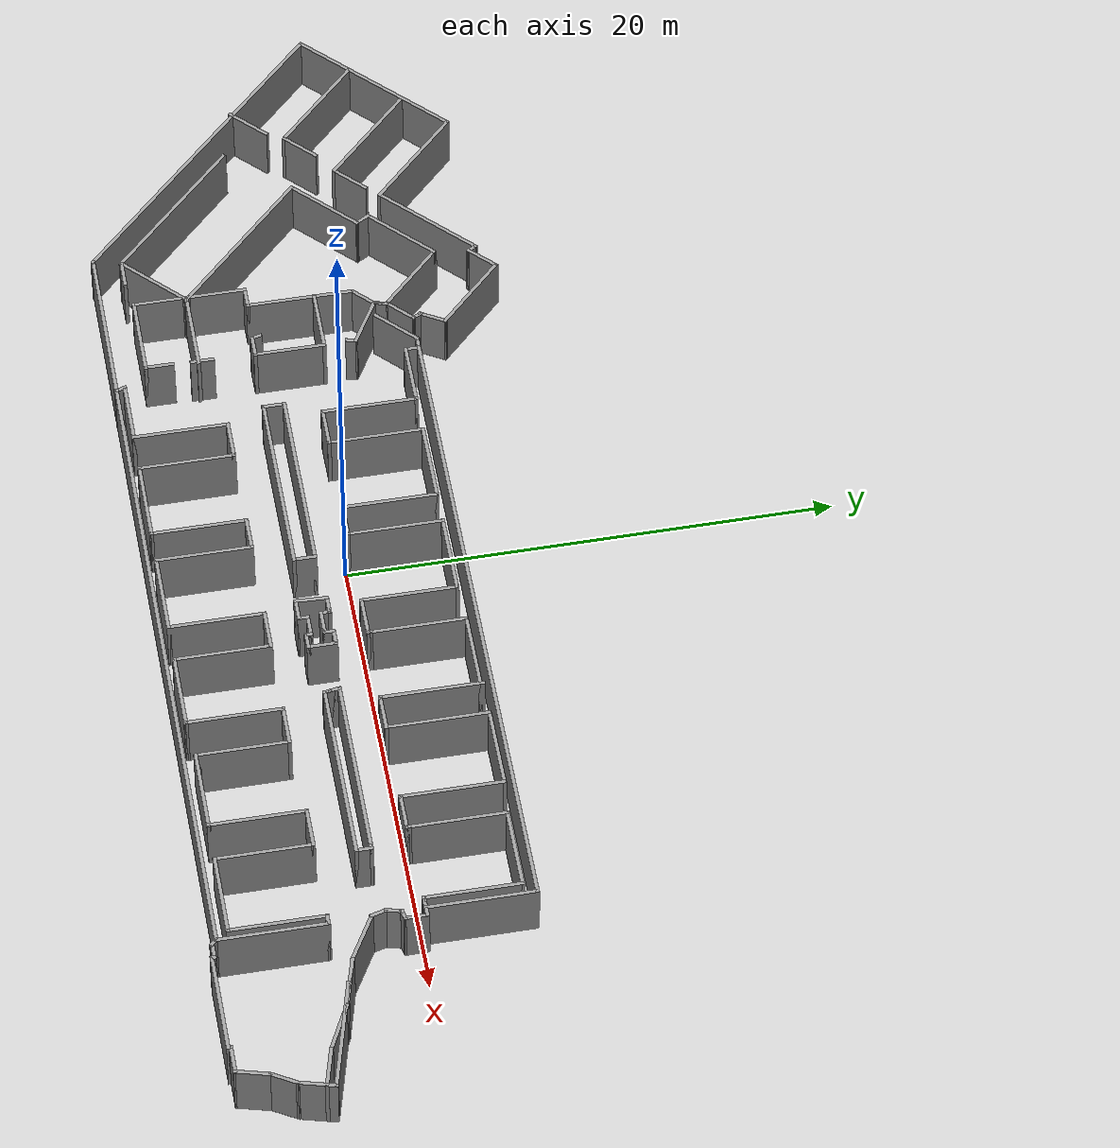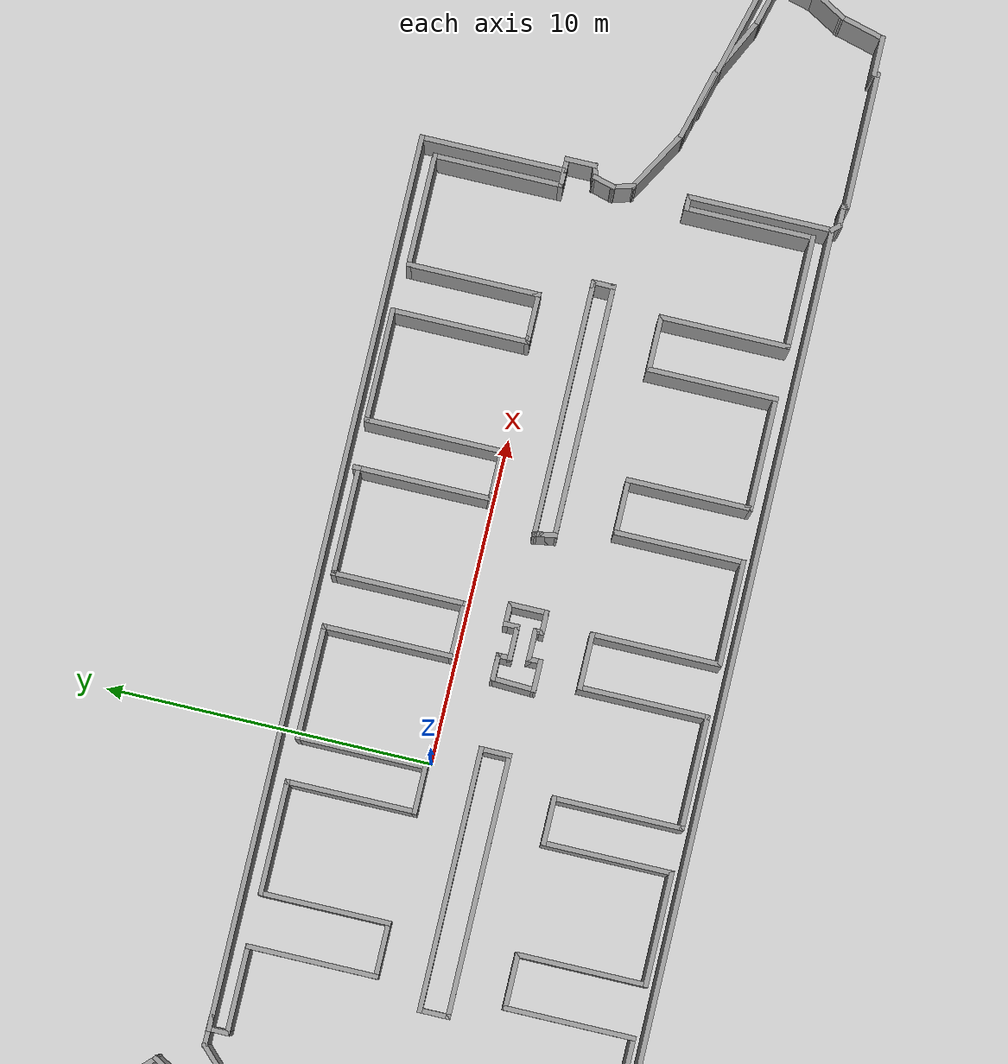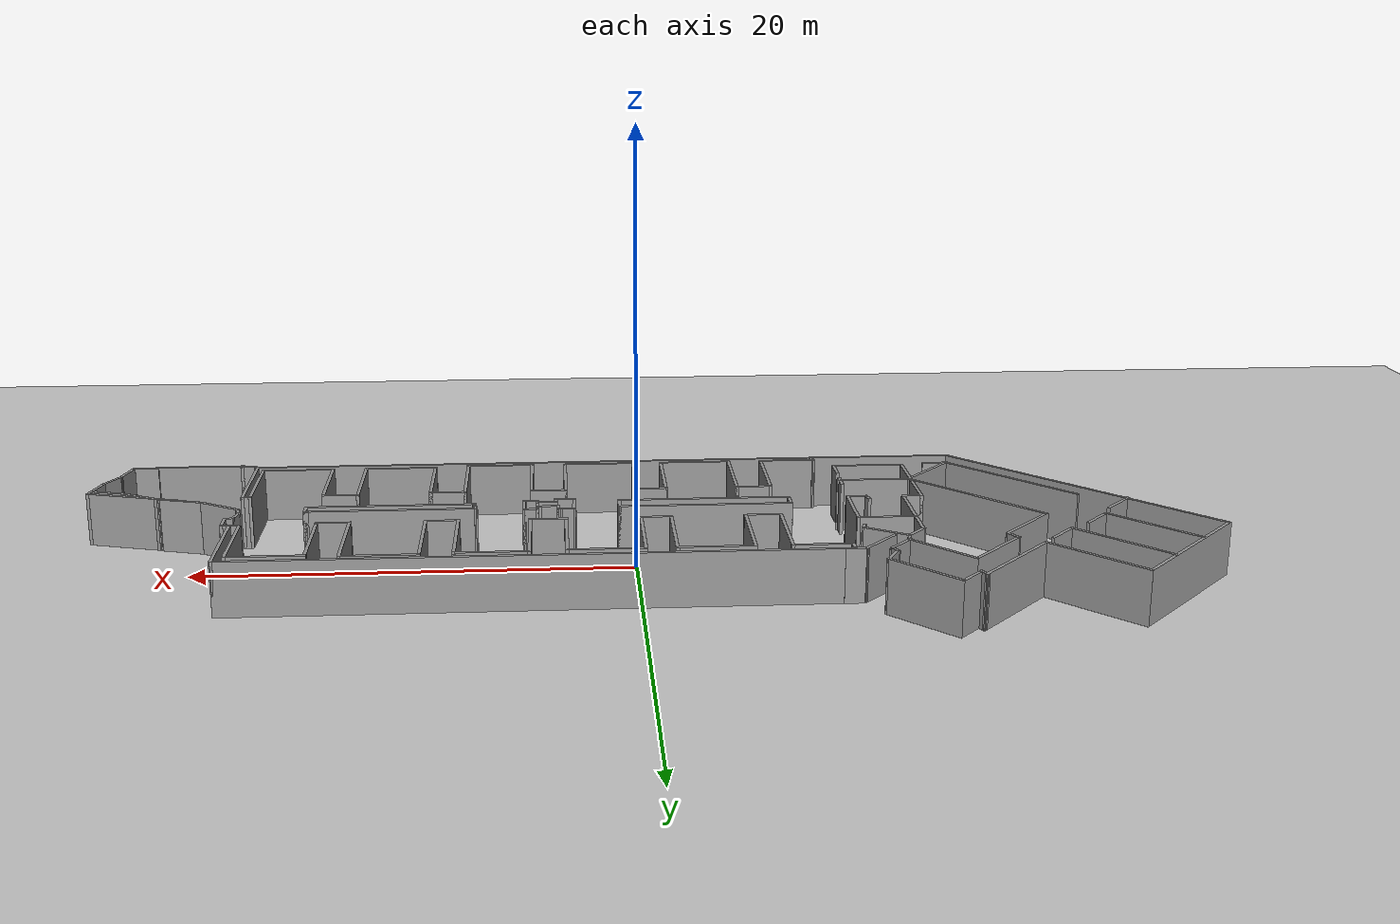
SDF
<sdf version="1.6">
 <world name="default">
  <light name="sun" type="directional">
   <pose>0 0 10 0 -0 0</pose>
   <diffuse>0.8 0.8 0.8 1</diffuse>
   <specular>0.2 0.2 0.2 1</specular>
   <attenuation>
    <range>1000</range>
    <constant>0.9</constant>
    <linear>0.01</linear>
    <quadratic>0.001</quadratic>
   </attenuation>
   <direction>-0.5 0.1 -0.9</direction>
  </light>
  <model name="ground_plane">
   <static>1</static>
   <link name="link">
    <collision name="collision">
     <geometry><plane><normal>0 0 1</normal><size>100 100</size></plane></geometry>
     <surface>
      <contact><collide_bitmask>65535</collide_bitmask></contact>
      <friction><ode><mu>100</mu><mu2>50</mu2></ode></friction>
     </surface>
    </collision>
    <visual name="visual">
     <cast_shadows>0</cast_shadows>
     <geometry><plane><normal>0 0 1</normal><size>100 100</size></plane></geometry>
     <material>
      <script><uri>file://media/materials/scripts/gazebo.material</uri><name>Gazebo/Grey</name></script>
     </material>
    </visual>
   </link>
  </model>
  <gravity>0 0 -9.8</gravity>
  <magnetic_field>6e-06 2.3e-05 -4.2e-05</magnetic_field>
  <atmosphere type="adiabatic"/>
  <physics name="default_physics" default="0" type="ode">
   <max_step_size>0.001</max_step_size>
   <real_time_factor>1</real_time_factor>
   <real_time_update_rate>1000</real_time_update_rate>
  </physics>
  <scene><ambient>0.4 0.4 0.4 1</ambient><background>0.7 0.7 0.7 1</background><shadows>1</shadows></scene>
  <spherical_coordinates>
   <surface_model>EARTH_WGS84</surface_model>
   <latitude_deg>0</latitude_deg>
   <longitude_deg>0</longitude_deg>
   <elevation>0</elevation>
   <heading_deg>0</heading_deg>
  </spherical_coordinates>
  <model name="planta">
   <pose>-0.447226 0.100458 0 0 -0 0</pose>
   <link name="Wall_1">
    <collision name="Wall_1_Collision">
     <geometry><box><size>8 0.15 2.5</size></box></geometry>
     <pose>0 0 1.25 0 -0 0</pose>
    </collision>
    <visual name="Wall_1_Visual">
     <pose>0 0 1.25 0 -0 0</pose>
     <geometry><box><size>8 0.15 2.5</size></box></geometry>
     <material>
      <script><uri>file://media/materials/scripts/gazebo.material</uri><name>Gazebo/Grey</name></script>
      <ambient>1 1 1 1</ambient>
     </material>
     <meta><layer>0</layer></meta>
    </visual>
    <pose>-2.78777 -1.43046 0 0 -0 0</pose>
   </link>
   <link name="Wall_10">
    <collision name="Wall_10_Collision">
     <geometry><box><size>0.25 0.15 2.5</size></box></geometry>
     <pose>0 0 1.25 0 -0 0</pose>
    </collision>
    <visual name="Wall_10_Visual">
     <pose>0 0 1.25 0 -0 0</pose>
     <geometry><box><size>0.25 0.15 2.5</size></box></geometry>
     <material>
      <script><uri>file://media/materials/scripts/gazebo.material</uri><name>Gazebo/Grey</name></script>
      <ambient>1 1 1 1</ambient>
     </material>
     <meta><layer>0</layer></meta>
    </visual>
    <pose>4.83723 -1.64046 0 0 -0 0</pose>
   </link>
   <link name="Wall_100">
    <collision name="Wall_100_Collision">
     <geometry><box><size>0.5 0.15 2.5</size></box></geometry>
     <pose>0 0 1.25 0 -0 0</pose>
    </collision>
    <visual name="Wall_100_Visual">
     <pose>0 0 1.25 0 -0 0</pose>
     <geometry><box><size>0.5 0.15 2.5</size></box></geometry>
     <material>
      <script><uri>file://media/materials/scripts/gazebo.material</uri><name>Gazebo/Grey</name></script>
      <ambient>1 1 1 1</ambient>
     </material>
     <meta><layer>0</layer></meta>
    </visual>
    <pose>18.6264 -0.800321 0 0 -0 -2.87979</pose>
   </link>
   <link name="Wall_101">
    <collision name="Wall_101_Collision">
     <geometry><box><size>0.75 0.15 2.5</size></box></geometry>
     <pose>0 0 1.25 0 -0 0</pose>
    </collision>
    <visual name="Wall_101_Visual">
     <pose>0 0 1.25 0 -0 0</pose>
     <geometry><box><size>0.75 0.15 2.5</size></box></geometry>
     <material>
      <script><uri>file://media/materials/scripts/gazebo.material</uri><name>Gazebo/Grey</name></script>
      <ambient>1 1 1 1</ambient>
     </material>
     <meta><layer>0</layer></meta>
    </visual>
    <pose>18.3798 -1.13539 0 0 -0 -1.8326</pose>
   </link>
   <link name="Wall_102">
    <collision name="Wall_102_Collision">
     <geometry><box><size>0.15 0.15 2.5</size></box></geometry>
     <pose>0 0 1.25 0 -0 0</pose>
    </collision>
    <visual name="Wall_102_Visual">
     <pose>0 0 1.25 0 -0 0</pose>
     <geometry><box><size>0.15 0.15 2.5</size></box></geometry>
     <material>
      <script><uri>file://media/materials/scripts/gazebo.material</uri><name>Gazebo/Grey</name></script>
      <ambient>1 1 1 1</ambient>
     </material>
     <meta><layer>0</layer></meta>
    </visual>
    <pose>18.3021 -1.42517 0 0 -0 0</pose>
   </link>
   <link name="Wall_103">
    <collision name="Wall_103_Collision">
     <geometry><box><size>0.75 0.15 2.5</size></box></geometry>
     <pose>0 0 1.25 0 -0 0</pose>
    </collision>
    <visual name="Wall_103_Visual">
     <pose>0 0 1.25 0 -0 0</pose>
     <geometry><box><size>0.75 0.15 2.5</size></box></geometry>
     <material>
      <script><uri>file://media/materials/scripts/gazebo.material</uri><name>Gazebo/Grey</name></script>
      <ambient>1 1 1 1</ambient>
     </material>
     <meta><layer>0</layer></meta>
    </visual>
    <pose>18.3798 -1.71495 0 0 -0 -1.309</pose>
   </link>
   <link name="Wall_104">
    <collision name="Wall_104_Collision">
     <geometry><box><size>2.25 0.15 2.5</size></box></geometry>
     <pose>0 0 1.25 0 -0 0</pose>
    </collision>
    <visual name="Wall_104_Visual">
     <pose>0 0 1.25 0 -0 0</pose>
     <geometry><box><size>2.25 0.15 2.5</size></box></geometry>
     <material>
      <script><uri>file://media/materials/scripts/gazebo.material</uri><name>Gazebo/Grey</name></script>
      <ambient>1 1 1 1</ambient>
     </material>
     <meta><layer>0</layer></meta>
    </visual>
    <pose>19.3667 -2.52973 0 0 -0 -0.523599</pose>
   </link>
   <link name="Wall_105">
    <collision name="Wall_105_Collision">
     <geometry><box><size>2.25 0.15 2.5</size></box></geometry>
     <pose>0 0 1.25 0 -0 0</pose>
    </collision>
    <visual name="Wall_105_Visual">
     <pose>0 0 1.25 0 -0 0</pose>
     <geometry><box><size>2.25 0.15 2.5</size></box></geometry>
     <material>
      <script><uri>file://media/materials/scripts/gazebo.material</uri><name>Gazebo/Grey</name></script>
      <ambient>1 1 1 1</ambient>
     </material>
     <meta><layer>0</layer></meta>
    </visual>
    <pose>21.2903 -3.32648 0 0 -0 -0.261799</pose>
   </link>
   <link name="Wall_107">
    <collision name="Wall_107_Collision">
     <geometry><box><size>4.75 0.15 2.5</size></box></geometry>
     <pose>0 0 1.25 0 -0 0</pose>
    </collision>
    <visual name="Wall_107_Visual">
     <pose>0 0 1.25 0 -0 0</pose>
     <geometry><box><size>4.75 0.15 2.5</size></box></geometry>
     <material>
      <script><uri>file://media/materials/scripts/gazebo.material</uri><name>Gazebo/Grey</name></script>
      <ambient>1 1 1 1</ambient>
     </material>
     <meta><layer>0</layer></meta>
    </visual>
    <pose>23.5471 -3.97871 0 0 -0 -0.261799</pose>
   </link>
   <link name="Wall_108">
    <collision name="Wall_108_Collision">
     <geometry><box><size>0.5 0.15 2.5</size></box></geometry>
     <pose>0 0 1.25 0 -0 0</pose>
    </collision>
    <visual name="Wall_108_Visual">
     <pose>0 0 1.25 0 -0 0</pose>
     <geometry><box><size>0.5 0.15 2.5</size></box></geometry>
     <material>
      <script><uri>file://media/materials/scripts/gazebo.material</uri><name>Gazebo/Grey</name></script>
      <ambient>1 1 1 1</ambient>
     </material>
     <meta><layer>0</layer></meta>
    </visual>
    <pose>25.7235 -4.74303 0 0 -0 -1.8326</pose>
   </link>
   <link name="Wall_109">
    <collision name="Wall_109_Collision">
     <geometry><box><size>1.75 0.15 2.5</size></box></geometry>
     <pose>0 0 1.25 0 -0 0</pose>
    </collision>
    <visual name="Wall_109_Visual">
     <pose>0 0 1.25 0 -0 0</pose>
     <geometry><box><size>1.75 0.15 2.5</size></box></geometry>
     <material>
      <script><uri>file://media/materials/scripts/gazebo.material</uri><name>Gazebo/Grey</name></script>
      <ambient>1 1 1 1</ambient>
     </material>
     <meta><layer>0</layer></meta>
    </visual>
    <pose>24.9055 -4.70501 0 0 -0 2.87979</pose>
   </link>
   <link name="Wall_11">
    <collision name="Wall_11_Collision">
     <geometry><box><size>0.5 0.15 2.5</size></box></geometry>
     <pose>0 0 1.25 0 -0 0</pose>
    </collision>
    <visual name="Wall_11_Visual">
     <pose>0 0 1.25 0 -0 0</pose>
     <geometry><box><size>0.5 0.15 2.5</size></box></geometry>
     <material>
      <script><uri>file://media/materials/scripts/gazebo.material</uri><name>Gazebo/Grey</name></script>
      <ambient>1 1 1 1</ambient>
     </material>
     <meta><layer>0</layer></meta>
    </visual>
    <pose>4.88723 -1.46546 0 0 -0 1.5708</pose>
   </link>
   <link name="Wall_110">
    <collision name="Wall_110_Collision">
     <geometry><box><size>2.18759 0.15 2.5</size></box></geometry>
     <pose>0 0 1.25 0 -0 0</pose>
    </collision>
    <visual name="Wall_110_Visual">
     <pose>0 0 1.25 0 -0 0</pose>
     <geometry><box><size>2.18759 0.15 2.5</size></box></geometry>
     <material>
      <script><uri>file://media/materials/scripts/gazebo.material</uri><name>Gazebo/Grey</name></script>
      <ambient>1 1 1 1</ambient>
     </material>
     <meta><layer>0</layer></meta>
    </visual>
    <pose>23.2186 -4.0481 0 0 -0 2.68426</pose>
   </link>
   <link name="Wall_111">
    <collision name="Wall_111_Collision">
     <geometry><box><size>1.5 0.15 2.5</size></box></geometry>
     <pose>0 0 1.25 0 -0 0</pose>
    </collision>
    <visual name="Wall_111_Visual">
     <pose>0 0 1.25 0 -0 0</pose>
     <geometry><box><size>1.5 0.15 2.5</size></box></geometry>
     <material>
      <script><uri>file://media/materials/scripts/gazebo.material</uri><name>Gazebo/Grey</name></script>
      <ambient>1 1 1 1</ambient>
     </material>
     <meta><layer>0</layer></meta>
    </visual>
    <pose>21.6525 -3.42354 0 0 -0 2.87979</pose>
   </link>
   <link name="Wall_113">
    <collision name="Wall_113_Collision">
     <geometry><box><size>1.25 0.15 2.5</size></box></geometry>
     <pose>0 0 1.25 0 -0 0</pose>
    </collision>
    <visual name="Wall_113_Visual">
     <pose>0 0 1.25 0 -0 0</pose>
     <geometry><box><size>1.25 0.15 2.5</size></box></geometry>
     <material>
      <script><uri>file://media/materials/scripts/gazebo.material</uri><name>Gazebo/Grey</name></script>
      <ambient>1 1 1 1</ambient>
     </material>
     <meta><layer>0</layer></meta>
    </visual>
    <pose>25.5358 -5.44332 0 0 -0 -1.8326</pose>
   </link>
   <link name="Wall_114">
    <collision name="Wall_114_Collision">
     <geometry><box><size>1.25 0.15 2.5</size></box></geometry>
     <pose>0 0 1.25 0 -0 0</pose>
    </collision>
    <visual name="Wall_114_Visual">
     <pose>0 0 1.25 0 -0 0</pose>
     <geometry><box><size>1.25 0.15 2.5</size></box></geometry>
     <material>
      <script><uri>file://media/materials/scripts/gazebo.material</uri><name>Gazebo/Grey</name></script>
      <ambient>1 1 1 1</ambient>
     </material>
     <meta><layer>0</layer></meta>
    </visual>
    <pose>25.1185 -6.4509 0 0 -0 -2.0944</pose>
   </link>
   <link name="Wall_115">
    <collision name="Wall_115_Collision">
     <geometry><box><size>1.5 0.15 2.5</size></box></geometry>
     <pose>0 0 1.25 0 -0 0</pose>
    </collision>
    <visual name="Wall_115_Visual">
     <pose>0 0 1.25 0 -0 0</pose>
     <geometry><box><size>1.5 0.15 2.5</size></box></geometry>
     <material>
      <script><uri>file://media/materials/scripts/gazebo.material</uri><name>Gazebo/Grey</name></script>
      <ambient>1 1 1 1</ambient>
     </material>
     <meta><layer>0</layer></meta>
    </visual>
    <pose>24.6688 -7.57921 0 0 -0 -1.8326</pose>
   </link>
   <link name="Wall_116">
    <collision name="Wall_116_Collision">
     <geometry><box><size>1.25 0.15 2.5</size></box></geometry>
     <pose>0 0 1.25 0 -0 0</pose>
    </collision>
    <visual name="Wall_116_Visual">
     <pose>0 0 1.25 0 -0 0</pose>
     <geometry><box><size>1.25 0.15 2.5</size></box></geometry>
     <material>
      <script><uri>file://media/materials/scripts/gazebo.material</uri><name>Gazebo/Grey</name></script>
      <ambient>1 1 1 1</ambient>
     </material>
     <meta><layer>0</layer></meta>
    </visual>
    <pose>23.9441 -8.23121 0 0 -0 3.14159</pose>
   </link>
   <link name="Wall_117">
    <collision name="Wall_117_Collision">
     <geometry><box><size>0.25 0.15 2.5</size></box></geometry>
     <pose>0 0 1.25 0 -0 0</pose>
    </collision>
    <visual name="Wall_117_Visual">
     <pose>0 0 1.25 0 -0 0</pose>
     <geometry><box><size>0.25 0.15 2.5</size></box></geometry>
     <material>
      <script><uri>file://media/materials/scripts/gazebo.material</uri><name>Gazebo/Grey</name></script>
      <ambient>1 1 1 1</ambient>
     </material>
     <meta><layer>0</layer></meta>
    </visual>
    <pose>23.3941 -8.28121 0 0 -0 -1.5708</pose>
   </link>
   <link name="Wall_118">
    <collision name="Wall_118_Collision">
     <geometry><box><size>4.25 0.15 2.5</size></box></geometry>
     <pose>0 0 1.25 0 -0 0</pose>
    </collision>
    <visual name="Wall_118_Visual">
     <pose>0 0 1.25 0 -0 0</pose>
     <geometry><box><size>4.25 0.15 2.5</size></box></geometry>
     <material>
      <script><uri>file://media/materials/scripts/gazebo.material</uri><name>Gazebo/Grey</name></script>
      <ambient>1 1 1 1</ambient>
     </material>
     <meta><layer>0</layer></meta>
    </visual>
    <pose>21.3441 -8.33121 0 0 -0 3.14159</pose>
   </link>
   <link name="Wall_119">
    <collision name="Wall_119_Collision">
     <geometry><box><size>0.25 0.15 2.5</size></box></geometry>
     <pose>0 0 1.25 0 -0 0</pose>
    </collision>
    <visual name="Wall_119_Visual">
     <pose>0 0 1.25 0 -0 0</pose>
     <geometry><box><size>0.25 0.15 2.5</size></box></geometry>
     <material>
      <script><uri>file://media/materials/scripts/gazebo.material</uri><name>Gazebo/Grey</name></script>
      <ambient>1 1 1 1</ambient>
     </material>
     <meta><layer>0</layer></meta>
    </visual>
    <pose>19.2941 -8.28121 0 0 -0 1.5708</pose>
   </link>
   <link name="Wall_12">
    <collision name="Wall_12_Collision">
     <geometry><box><size>0.75 0.15 2.5</size></box></geometry>
     <pose>0 0 1.25 0 -0 0</pose>
    </collision>
    <visual name="Wall_12_Visual">
     <pose>0 0 1.25 0 -0 0</pose>
     <geometry><box><size>0.75 0.15 2.5</size></box></geometry>
     <material>
      <script><uri>file://media/materials/scripts/gazebo.material</uri><name>Gazebo/Grey</name></script>
      <ambient>1 1 1 1</ambient>
     </material>
     <meta><layer>0</layer></meta>
    </visual>
    <pose>5.18722 -1.29046 0 0 -0 0</pose>
   </link>
   <link name="Wall_120">
    <collision name="Wall_120_Collision">
     <geometry><box><size>0.75 0.15 2.5</size></box></geometry>
     <pose>0 0 1.25 0 -0 0</pose>
    </collision>
    <visual name="Wall_120_Visual">
     <pose>0 0 1.25 0 -0 0</pose>
     <geometry><box><size>0.75 0.15 2.5</size></box></geometry>
     <material>
      <script><uri>file://media/materials/scripts/gazebo.material</uri><name>Gazebo/Grey</name></script>
      <ambient>1 1 1 1</ambient>
     </material>
     <meta><layer>0</layer></meta>
    </visual>
    <pose>18.9941 -8.23121 0 0 -0 3.14159</pose>
   </link>
   <link name="Wall_121">
    <collision name="Wall_121_Collision">
     <geometry><box><size>0.402483 0.15 2.5</size></box></geometry>
     <pose>0 0 1.25 0 -0 0</pose>
    </collision>
    <visual name="Wall_121_Visual">
     <pose>0 0 1.25 0 -0 0</pose>
     <geometry><box><size>0.402483 0.15 2.5</size></box></geometry>
     <material>
      <script><uri>file://media/materials/scripts/gazebo.material</uri><name>Gazebo/Grey</name></script>
      <ambient>1 1 1 1</ambient>
     </material>
     <meta><layer>0</layer></meta>
    </visual>
    <pose>18.6066 -8.14016 0 0 -0 2.33599</pose>
   </link>
   <link name="Wall_123">
    <collision name="Wall_123_Collision">
     <geometry><box><size>7 0.15 2.5</size></box></geometry>
     <pose>0 0 1.25 0 -0 0</pose>
    </collision>
    <visual name="Wall_123_Visual">
     <pose>0 0 1.25 0 -0 0</pose>
     <geometry><box><size>7 0.15 2.5</size></box></geometry>
     <material>
      <script><uri>file://media/materials/scripts/gazebo.material</uri><name>Gazebo/Grey</name></script>
      <ambient>1 1 1 1</ambient>
     </material>
     <meta><layer>0</layer></meta>
    </visual>
    <pose>-12.0058 -8.04911 0 0 -0 3.14159</pose>
   </link>
   <link name="Wall_125">
    <collision name="Wall_125_Collision">
     <geometry><box><size>14.75 0.15 2.5</size></box></geometry>
     <pose>0 0 1.25 0 -0 0</pose>
    </collision>
    <visual name="Wall_125_Visual">
     <pose>0 0 1.25 0 -0 0</pose>
     <geometry><box><size>14.75 0.15 2.5</size></box></geometry>
     <material>
      <script><uri>file://media/materials/scripts/gazebo.material</uri><name>Gazebo/Grey</name></script>
      <ambient>1 1 1 1</ambient>
     </material>
     <meta><layer>0</layer></meta>
    </visual>
    <pose>-20.5927 -2.88723 0 0 -0 2.35619</pose>
   </link>
   <link name="Wall_126">
    <collision name="Wall_126_Collision">
     <geometry><box><size>7.75 0.15 2.5</size></box></geometry>
     <pose>0 0 1.25 0 -0 0</pose>
    </collision>
    <visual name="Wall_126_Visual">
     <pose>0 0 1.25 0 -0 0</pose>
     <geometry><box><size>7.75 0.15 2.5</size></box></geometry>
     <material>
      <script><uri>file://media/materials/scripts/gazebo.material</uri><name>Gazebo/Grey</name></script>
      <ambient>1 1 1 1</ambient>
     </material>
     <meta><layer>0</layer></meta>
    </visual>
    <pose>-23.0676 4.96166 0 0 -0 0.785398</pose>
   </link>
   <link name="Wall_127">
    <collision name="Wall_127_Collision">
     <geometry><box><size>5 0.15 2.5</size></box></geometry>
     <pose>0 0 1.25 0 -0 0</pose>
    </collision>
    <visual name="Wall_127_Visual">
     <pose>0 0 1.25 0 -0 0</pose>
     <geometry><box><size>5 0.15 2.5</size></box></geometry>
     <material>
      <script><uri>file://media/materials/scripts/gazebo.material</uri><name>Gazebo/Grey</name></script>
      <ambient>1 1 1 1</ambient>
     </material>
     <meta><layer>0</layer></meta>
    </visual>
    <pose>-18.6658 5.93393 0 0 -0 -0.785398</pose>
   </link>
   <link name="Wall_128">
    <collision name="Wall_128_Collision">
     <geometry><box><size>5 0.15 2.5</size></box></geometry>
     <pose>0 0 1.25 0 -0 0</pose>
    </collision>
    <visual name="Wall_128_Visual">
     <pose>0 0 1.25 0 -0 0</pose>
     <geometry><box><size>5 0.15 2.5</size></box></geometry>
     <material>
      <script><uri>file://media/materials/scripts/gazebo.material</uri><name>Gazebo/Grey</name></script>
      <ambient>1 1 1 1</ambient>
     </material>
     <meta><layer>0</layer></meta>
    </visual>
    <pose>-15.2364 5.93393 0 0 -0 0.785398</pose>
   </link>
   <link name="Wall_129">
    <collision name="Wall_129_Collision">
     <geometry><box><size>0.5 0.15 2.5</size></box></geometry>
     <pose>0 0 1.25 0 -0 0</pose>
    </collision>
    <visual name="Wall_129_Visual">
     <pose>0 0 1.25 0 -0 0</pose>
     <geometry><box><size>0.5 0.15 2.5</size></box></geometry>
     <material>
      <script><uri>file://media/materials/scripts/gazebo.material</uri><name>Gazebo/Grey</name></script>
      <ambient>1 1 1 1</ambient>
     </material>
     <meta><layer>0</layer></meta>
    </visual>
    <pose>-13.4341 7.49711 0 0 -0 -1.0472</pose>
   </link>
   <link name="Wall_13">
    <collision name="Wall_13_Collision">
     <geometry><box><size>1.25 0.15 2.5</size></box></geometry>
     <pose>0 0 1.25 0 -0 0</pose>
    </collision>
    <visual name="Wall_13_Visual">
     <pose>0 0 1.25 0 -0 0</pose>
     <geometry><box><size>1.25 0.15 2.5</size></box></geometry>
     <material>
      <script><uri>file://media/materials/scripts/gazebo.material</uri><name>Gazebo/Grey</name></script>
      <ambient>1 1 1 1</ambient>
     </material>
     <meta><layer>0</layer></meta>
    </visual>
    <pose>5.48723 -1.84046 0 0 -0 -1.5708</pose>
   </link>
   <link name="Wall_130">
    <collision name="Wall_130_Collision">
     <geometry><box><size>1.5 0.15 2.5</size></box></geometry>
     <pose>0 0 1.25 0 -0 0</pose>
    </collision>
    <visual name="Wall_130_Visual">
     <pose>0 0 1.25 0 -0 0</pose>
     <geometry><box><size>1.5 0.15 2.5</size></box></geometry>
     <material>
      <script><uri>file://media/materials/scripts/gazebo.material</uri><name>Gazebo/Grey</name></script>
      <ambient>1 1 1 1</ambient>
     </material>
     <meta><layer>0</layer></meta>
    </visual>
    <pose>-12.8693 7.82285 0 0 -0 0.785398</pose>
   </link>
   <link name="Wall_131">
    <collision name="Wall_131_Collision">
     <geometry><box><size>3.75 0.15 2.5</size></box></geometry>
     <pose>0 0 1.25 0 -0 0</pose>
    </collision>
    <visual name="Wall_131_Visual">
     <pose>0 0 1.25 0 -0 0</pose>
     <geometry><box><size>3.75 0.15 2.5</size></box></geometry>
     <material>
      <script><uri>file://media/materials/scripts/gazebo.material</uri><name>Gazebo/Grey</name></script>
      <ambient>1 1 1 1</ambient>
     </material>
     <meta><layer>0</layer></meta>
    </visual>
    <pose>-11.1192 7.02735 0 0 -0 -0.785398</pose>
   </link>
   <link name="Wall_132">
    <collision name="Wall_132_Collision">
     <geometry><box><size>1.25 0.15 2.5</size></box></geometry>
     <pose>0 0 1.25 0 -0 0</pose>
    </collision>
    <visual name="Wall_132_Visual">
     <pose>0 0 1.25 0 -0 0</pose>
     <geometry><box><size>1.25 0.15 2.5</size></box></geometry>
     <material>
      <script><uri>file://media/materials/scripts/gazebo.material</uri><name>Gazebo/Grey</name></script>
      <ambient>1 1 1 1</ambient>
     </material>
     <meta><layer>0</layer></meta>
    </visual>
    <pose>-10.1214 5.27825 0 0 -0 -2.0944</pose>
   </link>
   <link name="Wall_133">
    <collision name="Wall_133_Collision">
     <geometry><box><size>0.5 0.15 2.5</size></box></geometry>
     <pose>0 0 1.25 0 -0 0</pose>
    </collision>
    <visual name="Wall_133_Visual">
     <pose>0 0 1.25 0 -0 0</pose>
     <geometry><box><size>0.5 0.15 2.5</size></box></geometry>
     <material>
      <script><uri>file://media/materials/scripts/gazebo.material</uri><name>Gazebo/Grey</name></script>
      <ambient>1 1 1 1</ambient>
     </material>
     <meta><layer>0</layer></meta>
    </visual>
    <pose>-10.3089 4.65038 0 0 -0 -1.0472</pose>
   </link>
   <link name="Wall_134">
    <collision name="Wall_134_Collision">
     <geometry><box><size>1.5 0.15 2.5</size></box></geometry>
     <pose>0 0 1.25 0 -0 0</pose>
    </collision>
    <visual name="Wall_134_Visual">
     <pose>0 0 1.25 0 -0 0</pose>
     <geometry><box><size>1.5 0.15 2.5</size></box></geometry>
     <material>
      <script><uri>file://media/materials/scripts/gazebo.material</uri><name>Gazebo/Grey</name></script>
      <ambient>1 1 1 1</ambient>
     </material>
     <meta><layer>0</layer></meta>
    </visual>
    <pose>-10.6987 4.02153 0 0 -0 -2.35619</pose>
   </link>
   <link name="Wall_135">
    <collision name="Wall_135_Collision">
     <geometry><box><size>3.5 0.15 2.5</size></box></geometry>
     <pose>0 0 1.25 0 -0 0</pose>
    </collision>
    <visual name="Wall_135_Visual">
     <pose>0 0 1.25 0 -0 0</pose>
     <geometry><box><size>3.5 0.15 2.5</size></box></geometry>
     <material>
      <script><uri>file://media/materials/scripts/gazebo.material</uri><name>Gazebo/Grey</name></script>
      <ambient>1 1 1 1</ambient>
     </material>
     <meta><layer>0</layer></meta>
    </visual>
    <pose>-12.3604 4.72863 0 0 -0 2.35619</pose>
   </link>
   <link name="Wall_136">
    <collision name="Wall_136_Collision">
     <geometry><box><size>3.5 0.15 2.5</size></box></geometry>
     <pose>0 0 1.25 0 -0 0</pose>
    </collision>
    <visual name="Wall_136_Visual">
     <pose>0 0 1.25 0 -0 0</pose>
     <geometry><box><size>3.5 0.15 2.5</size></box></geometry>
     <material>
      <script><uri>file://media/materials/scripts/gazebo.material</uri><name>Gazebo/Grey</name></script>
      <ambient>1 1 1 1</ambient>
     </material>
     <meta><layer>0</layer></meta>
    </visual>
    <pose>-14.7292 4.72863 0 0 -0 -2.35619</pose>
   </link>
   <link name="Wall_137">
    <collision name="Wall_137_Collision">
     <geometry><box><size>0.75 0.15 2.5</size></box></geometry>
     <pose>0 0 1.25 0 -0 0</pose>
    </collision>
    <visual name="Wall_137_Visual">
     <pose>0 0 1.25 0 -0 0</pose>
     <geometry><box><size>0.75 0.15 2.5</size></box></geometry>
     <material>
      <script><uri>file://media/materials/scripts/gazebo.material</uri><name>Gazebo/Grey</name></script>
      <ambient>1 1 1 1</ambient>
     </material>
     <meta><layer>0</layer></meta>
    </visual>
    <pose>-15.7636 3.28442 0 0 -0 -1.0472</pose>
   </link>
   <link name="Wall_138">
    <collision name="Wall_138_Collision">
     <geometry><box><size>3.5 0.15 2.5</size></box></geometry>
     <pose>0 0 1.25 0 -0 0</pose>
    </collision>
    <visual name="Wall_138_Visual">
     <pose>0 0 1.25 0 -0 0</pose>
     <geometry><box><size>3.5 0.15 2.5</size></box></geometry>
     <material>
      <script><uri>file://media/materials/scripts/gazebo.material</uri><name>Gazebo/Grey</name></script>
      <ambient>1 1 1 1</ambient>
     </material>
     <meta><layer>0</layer></meta>
    </visual>
    <pose>-16.7981 1.84021 0 0 -0 -2.35619</pose>
   </link>
   <link name="Wall_139">
    <collision name="Wall_139_Collision">
     <geometry><box><size>7.5 0.15 2.5</size></box></geometry>
     <pose>0 0 1.25 0 -0 0</pose>
    </collision>
    <visual name="Wall_139_Visual">
     <pose>0 0 1.25 0 -0 0</pose>
     <geometry><box><size>7.5 0.15 2.5</size></box></geometry>
     <material>
      <script><uri>file://media/materials/scripts/gazebo.material</uri><name>Gazebo/Grey</name></script>
      <ambient>1 1 1 1</ambient>
     </material>
     <meta><layer>0</layer></meta>
    </visual>
    <pose>-15.3838 -1.94281 0 0 -0 -0.785398</pose>
   </link>
   <link name="Wall_14">
    <collision name="Wall_14_Collision">
     <geometry><box><size>0.75 0.15 2.5</size></box></geometry>
     <pose>0 0 1.25 0 -0 0</pose>
    </collision>
    <visual name="Wall_14_Visual">
     <pose>0 0 1.25 0 -0 0</pose>
     <geometry><box><size>0.75 0.15 2.5</size></box></geometry>
     <material>
      <script><uri>file://media/materials/scripts/gazebo.material</uri><name>Gazebo/Grey</name></script>
      <ambient>1 1 1 1</ambient>
     </material>
     <meta><layer>0</layer></meta>
    </visual>
    <pose>5.18722 -2.39046 0 0 -0 3.14159</pose>
   </link>
   <link name="Wall_140">
    <collision name="Wall_140_Collision">
     <geometry><box><size>3.5 0.15 2.5</size></box></geometry>
     <pose>0 0 1.25 0 -0 0</pose>
    </collision>
    <visual name="Wall_140_Visual">
     <pose>0 0 1.25 0 -0 0</pose>
     <geometry><box><size>3.5 0.15 2.5</size></box></geometry>
     <material>
      <script><uri>file://media/materials/scripts/gazebo.material</uri><name>Gazebo/Grey</name></script>
      <ambient>1 1 1 1</ambient>
     </material>
     <meta><layer>0</layer></meta>
    </visual>
    <pose>-13.9696 -5.72583 0 0 -0 -2.35619</pose>
   </link>
   <link name="Wall_141">
    <collision name="Wall_141_Collision">
     <geometry><box><size>7.25 0.15 2.5</size></box></geometry>
     <pose>0 0 1.25 0 -0 0</pose>
    </collision>
    <visual name="Wall_141_Visual">
     <pose>0 0 1.25 0 -0 0</pose>
     <geometry><box><size>7.25 0.15 2.5</size></box></geometry>
     <material>
      <script><uri>file://media/materials/scripts/gazebo.material</uri><name>Gazebo/Grey</name></script>
      <ambient>1 1 1 1</ambient>
     </material>
     <meta><layer>0</layer></meta>
    </visual>
    <pose>-17.6643 -4.40001 0 0 -0 2.35619</pose>
   </link>
   <link name="Wall_143">
    <collision name="Wall_143_Collision">
     <geometry><box><size>2 0.15 2.5</size></box></geometry>
     <pose>0 0 1.25 0 -0 0</pose>
    </collision>
    <visual name="Wall_143_Visual">
     <pose>0 0 1.25 0 -0 0</pose>
     <geometry><box><size>2 0.15 2.5</size></box></geometry>
     <material>
      <script><uri>file://media/materials/scripts/gazebo.material</uri><name>Gazebo/Grey</name></script>
      <ambient>1 1 1 1</ambient>
     </material>
     <meta><layer>0</layer></meta>
    </visual>
    <pose>-21.7238 -0.595709 0 0 -0 0.785398</pose>
   </link>
   <link name="Wall_145">
    <collision name="Wall_145_Collision">
     <geometry><box><size>1.75 0.15 2.5</size></box></geometry>
     <pose>0 0 1.25 0 -0 0</pose>
    </collision>
    <visual name="Wall_145_Visual">
     <pose>0 0 1.25 0 -0 0</pose>
     <geometry><box><size>1.75 0.15 2.5</size></box></geometry>
     <material>
      <script><uri>file://media/materials/scripts/gazebo.material</uri><name>Gazebo/Grey</name></script>
      <ambient>1 1 1 1</ambient>
     </material>
     <meta><layer>0</layer></meta>
    </visual>
    <pose>-20.1131 1.33868 0 0 -0 0.785398</pose>
   </link>
   <link name="Wall_147">
    <collision name="Wall_147_Collision">
     <geometry><box><size>1.75 0.15 2.5</size></box></geometry>
     <pose>0 0 1.25 0 -0 0</pose>
    </collision>
    <visual name="Wall_147_Visual">
     <pose>0 0 1.25 0 -0 0</pose>
     <geometry><box><size>1.75 0.15 2.5</size></box></geometry>
     <material>
      <script><uri>file://media/materials/scripts/gazebo.material</uri><name>Gazebo/Grey</name></script>
      <ambient>1 1 1 1</ambient>
     </material>
     <meta><layer>0</layer></meta>
    </visual>
    <pose>-18.008 3.12011 0 0 -0 -2.35619</pose>
   </link>
   <link name="Wall_148">
    <collision name="Wall_148_Collision">
     <geometry><box><size>5 0.15 2.5</size></box></geometry>
     <pose>0 0 1.25 0 -0 0</pose>
    </collision>
    <visual name="Wall_148_Visual">
     <pose>0 0 1.25 0 -0 0</pose>
     <geometry><box><size>5 0.15 2.5</size></box></geometry>
     <material>
      <script><uri>file://media/materials/scripts/gazebo.material</uri><name>Gazebo/Grey</name></script>
      <ambient>1 1 1 1</ambient>
     </material>
     <meta><layer>0</layer></meta>
    </visual>
    <pose>-20.2884 4.26916 0 0 -0 2.35619</pose>
   </link>
   <link name="Wall_15">
    <collision name="Wall_15_Collision">
     <geometry><box><size>0.15 0.15 2.5</size></box></geometry>
     <pose>0 0 1.25 0 -0 0</pose>
    </collision>
    <visual name="Wall_15_Visual">
     <pose>0 0 1.25 0 -0 0</pose>
     <geometry><box><size>0.15 0.15 2.5</size></box></geometry>
     <material>
      <script><uri>file://media/materials/scripts/gazebo.material</uri><name>Gazebo/Grey</name></script>
      <ambient>1 1 1 1</ambient>
     </material>
     <meta><layer>0</layer></meta>
    </visual>
    <pose>4.88723 -2.39046 0 0 -0 0</pose>
   </link>
   <link name="Wall_150">
    <collision name="Wall_150_Collision">
     <geometry><box><size>4.75 0.15 2.5</size></box></geometry>
     <pose>0 0 1.25 0 -0 0</pose>
    </collision>
    <visual name="Wall_150_Visual">
     <pose>0 0 1.25 0 -0 0</pose>
     <geometry><box><size>4.75 0.15 2.5</size></box></geometry>
     <material>
      <script><uri>file://media/materials/scripts/gazebo.material</uri><name>Gazebo/Grey</name></script>
      <ambient>1 1 1 1</ambient>
     </material>
     <meta><layer>0</layer></meta>
    </visual>
    <pose>-22.3051 2.39934 0 0 -0 2.35619</pose>
   </link>
   <link name="Wall_153">
    <collision name="Wall_153_Collision">
     <geometry><box><size>1.25 0.15 2.5</size></box></geometry>
     <pose>0 0 1.25 0 -0 0</pose>
    </collision>
    <visual name="Wall_153_Visual">
     <pose>0 0 1.25 0 -0 0</pose>
     <geometry><box><size>1.25 0.15 2.5</size></box></geometry>
     <material>
      <script><uri>file://media/materials/scripts/gazebo.material</uri><name>Gazebo/Grey</name></script>
      <ambient>1 1 1 1</ambient>
     </material>
     <meta><layer>0</layer></meta>
    </visual>
    <pose>-14.604 -6.91024 0 0 -0 0</pose>
   </link>
   <link name="Wall_155">
    <collision name="Wall_155_Collision">
     <geometry><box><size>3.5 0.15 2.5</size></box></geometry>
     <pose>0 0 1.25 0 -0 0</pose>
    </collision>
    <visual name="Wall_155_Visual">
     <pose>0 0 1.25 0 -0 0</pose>
     <geometry><box><size>3.5 0.15 2.5</size></box></geometry>
     <material>
      <script><uri>file://media/materials/scripts/gazebo.material</uri><name>Gazebo/Grey</name></script>
      <ambient>1 1 1 1</ambient>
     </material>
     <meta><layer>0</layer></meta>
    </visual>
    <pose>-11.2285 -6.71129 0 0 -0 3.14159</pose>
   </link>
   <link name="Wall_156">
    <collision name="Wall_156_Collision">
     <geometry><box><size>4.75 0.15 2.5</size></box></geometry>
     <pose>0 0 1.25 0 -0 0</pose>
    </collision>
    <visual name="Wall_156_Visual">
     <pose>0 0 1.25 0 -0 0</pose>
     <geometry><box><size>4.75 0.15 2.5</size></box></geometry>
     <material>
      <script><uri>file://media/materials/scripts/gazebo.material</uri><name>Gazebo/Grey</name></script>
      <ambient>1 1 1 1</ambient>
     </material>
     <meta><layer>0</layer></meta>
    </visual>
    <pose>-12.9035 -4.41129 0 0 -0 1.5708</pose>
   </link>
   <link name="Wall_157">
    <collision name="Wall_157_Collision">
     <geometry><box><size>1 0.15 2.5</size></box></geometry>
     <pose>0 0 1.25 0 -0 0</pose>
    </collision>
    <visual name="Wall_157_Visual">
     <pose>0 0 1.25 0 -0 0</pose>
     <geometry><box><size>1 0.15 2.5</size></box></geometry>
     <material>
      <script><uri>file://media/materials/scripts/gazebo.material</uri><name>Gazebo/Grey</name></script>
      <ambient>1 1 1 1</ambient>
     </material>
     <meta><layer>0</layer></meta>
    </visual>
    <pose>-12.4785 -2.11129 0 0 -0 0</pose>
   </link>
   <link name="Wall_158">
    <collision name="Wall_158_Collision">
     <geometry><box><size>4.5 0.15 2.5</size></box></geometry>
     <pose>0 0 1.25 0 -0 0</pose>
    </collision>
    <visual name="Wall_158_Visual">
     <pose>0 0 1.25 0 -0 0</pose>
     <geometry><box><size>4.5 0.15 2.5</size></box></geometry>
     <material>
      <script><uri>file://media/materials/scripts/gazebo.material</uri><name>Gazebo/Grey</name></script>
      <ambient>1 1 1 1</ambient>
     </material>
     <meta><layer>0</layer></meta>
    </visual>
    <pose>-12.0535 0.063714 0 0 -0 1.5708</pose>
   </link>
   <link name="Wall_159">
    <collision name="Wall_159_Collision">
     <geometry><box><size>1.25 0.15 2.5</size></box></geometry>
     <pose>0 0 1.25 0 -0 0</pose>
    </collision>
    <visual name="Wall_159_Visual">
     <pose>0 0 1.25 0 -0 0</pose>
     <geometry><box><size>1.25 0.15 2.5</size></box></geometry>
     <material>
      <script><uri>file://media/materials/scripts/gazebo.material</uri><name>Gazebo/Grey</name></script>
      <ambient>1 1 1 1</ambient>
     </material>
     <meta><layer>0</layer></meta>
    </visual>
    <pose>-11.6646 2.62762 0 0 -0 0.785398</pose>
   </link>
   <link name="Wall_16">
    <collision name="Wall_16_Collision">
     <geometry><box><size>0.15 0.15 2.5</size></box></geometry>
     <pose>0 0 1.25 0 -0 0</pose>
    </collision>
    <visual name="Wall_16_Visual">
     <pose>0 0 1.25 0 -0 0</pose>
     <geometry><box><size>0.15 0.15 2.5</size></box></geometry>
     <material>
      <script><uri>file://media/materials/scripts/gazebo.material</uri><name>Gazebo/Grey</name></script>
      <ambient>1 1 1 1</ambient>
     </material>
     <meta><layer>0</layer></meta>
    </visual>
    <pose>4.88723 -2.39046 0 0 -0 0</pose>
   </link>
   <link name="Wall_160">
    <collision name="Wall_160_Collision">
     <geometry><box><size>0.687025 0.15 2.5</size></box></geometry>
     <pose>0 0 1.25 0 -0 0</pose>
    </collision>
    <visual name="Wall_160_Visual">
     <pose>0 0 1.25 0 -0 0</pose>
     <geometry><box><size>0.687025 0.15 2.5</size></box></geometry>
     <material>
      <script><uri>file://media/materials/scripts/gazebo.material</uri><name>Gazebo/Grey</name></script>
      <ambient>1 1 1 1</ambient>
     </material>
     <meta><layer>0</layer></meta>
    </visual>
    <pose>-11.2259 3.28038 0 0 -0 1.38416</pose>
   </link>
   <link name="Wall_161">
    <collision name="Wall_161_Collision">
     <geometry><box><size>0.687025 0.15 2.5</size></box></geometry>
     <pose>0 0 1.25 0 -0 0</pose>
    </collision>
    <visual name="Wall_161_Visual">
     <pose>0 0 1.25 0 -0 0</pose>
     <geometry><box><size>0.687025 0.15 2.5</size></box></geometry>
     <material>
      <script><uri>file://media/materials/scripts/gazebo.material</uri><name>Gazebo/Grey</name></script>
      <ambient>1 1 1 1</ambient>
     </material>
     <meta><layer>0</layer></meta>
    </visual>
    <pose>-11.2259 3.28038 0 0 -0 -1.75743</pose>
   </link>
   <link name="Wall_162">
    <collision name="Wall_162_Collision">
     <geometry><box><size>2.25 0.15 2.5</size></box></geometry>
     <pose>0 0 1.25 0 -0 0</pose>
    </collision>
    <visual name="Wall_162_Visual">
     <pose>0 0 1.25 0 -0 0</pose>
     <geometry><box><size>2.25 0.15 2.5</size></box></geometry>
     <material>
      <script><uri>file://media/materials/scripts/gazebo.material</uri><name>Gazebo/Grey</name></script>
      <ambient>1 1 1 1</ambient>
     </material>
     <meta><layer>0</layer></meta>
    </visual>
    <pose>-10.3664 2.49153 0 0 -0 -0.523599</pose>
   </link>
   <link name="Wall_163">
    <collision name="Wall_163_Collision">
     <geometry><box><size>0.5 0.15 2.5</size></box></geometry>
     <pose>0 0 1.25 0 -0 0</pose>
    </collision>
    <visual name="Wall_163_Visual">
     <pose>0 0 1.25 0 -0 0</pose>
     <geometry><box><size>0.5 0.15 2.5</size></box></geometry>
     <material>
      <script><uri>file://media/materials/scripts/gazebo.material</uri><name>Gazebo/Grey</name></script>
      <ambient>1 1 1 1</ambient>
     </material>
     <meta><layer>0</layer></meta>
    </visual>
    <pose>-9.50232 1.79749 0 0 -0 -1.8326</pose>
   </link>
   <link name="Wall_165">
    <collision name="Wall_165_Collision">
     <geometry><box><size>2.75 0.15 2.5</size></box></geometry>
     <pose>0 0 1.25 0 -0 0</pose>
    </collision>
    <visual name="Wall_165_Visual">
     <pose>0 0 1.25 0 -0 0</pose>
     <geometry><box><size>2.75 0.15 2.5</size></box></geometry>
     <material>
      <script><uri>file://media/materials/scripts/gazebo.material</uri><name>Gazebo/Grey</name></script>
      <ambient>1 1 1 1</ambient>
     </material>
     <meta><layer>0</layer></meta>
    </visual>
    <pose>-10.7617 0.651629 0 0 -0 0</pose>
   </link>
   <link name="Wall_166">
    <collision name="Wall_166_Collision">
     <geometry><box><size>3 0.15 2.5</size></box></geometry>
     <pose>0 0 1.25 0 -0 0</pose>
    </collision>
    <visual name="Wall_166_Visual">
     <pose>0 0 1.25 0 -0 0</pose>
     <geometry><box><size>3 0.15 2.5</size></box></geometry>
     <material>
      <script><uri>file://media/materials/scripts/gazebo.material</uri><name>Gazebo/Grey</name></script>
      <ambient>1 1 1 1</ambient>
     </material>
     <meta><layer>0</layer></meta>
    </visual>
    <pose>-9.46174 -0.773371 0 0 -0 -1.5708</pose>
   </link>
   <link name="Wall_167">
    <collision name="Wall_167_Collision">
     <geometry><box><size>1 0.15 2.5</size></box></geometry>
     <pose>0 0 1.25 0 -0 0</pose>
    </collision>
    <visual name="Wall_167_Visual">
     <pose>0 0 1.25 0 -0 0</pose>
     <geometry><box><size>1 0.15 2.5</size></box></geometry>
     <material>
      <script><uri>file://media/materials/scripts/gazebo.material</uri><name>Gazebo/Grey</name></script>
      <ambient>1 1 1 1</ambient>
     </material>
     <meta><layer>0</layer></meta>
    </visual>
    <pose>-9.88674 -2.19837 0 0 -0 3.14159</pose>
   </link>
   <link name="Wall_168">
    <collision name="Wall_168_Collision">
     <geometry><box><size>0.5 0.15 2.5</size></box></geometry>
     <pose>0 0 1.25 0 -0 0</pose>
    </collision>
    <visual name="Wall_168_Visual">
     <pose>0 0 1.25 0 -0 0</pose>
     <geometry><box><size>0.5 0.15 2.5</size></box></geometry>
     <material>
      <script><uri>file://media/materials/scripts/gazebo.material</uri><name>Gazebo/Grey</name></script>
      <ambient>1 1 1 1</ambient>
     </material>
     <meta><layer>0</layer></meta>
    </visual>
    <pose>-10.357 -2.02933 0 0 -0 1.8326</pose>
   </link>
   <link name="Wall_17">
    <collision name="Wall_17_Collision">
     <geometry><box><size>0.25 0.15 2.5</size></box></geometry>
     <pose>0 0 1.25 0 -0 0</pose>
    </collision>
    <visual name="Wall_17_Visual">
     <pose>0 0 1.25 0 -0 0</pose>
     <geometry><box><size>0.25 0.15 2.5</size></box></geometry>
     <material>
      <script><uri>file://media/materials/scripts/gazebo.material</uri><name>Gazebo/Grey</name></script>
      <ambient>1 1 1 1</ambient>
     </material>
     <meta><layer>0</layer></meta>
    </visual>
    <pose>4.88723 -2.34046 0 0 -0 1.5708</pose>
   </link>
   <link name="Wall_170">
    <collision name="Wall_170_Collision">
     <geometry><box><size>1.25 0.15 2.5</size></box></geometry>
     <pose>0 0 1.25 0 -0 0</pose>
    </collision>
    <visual name="Wall_170_Visual">
     <pose>0 0 1.25 0 -0 0</pose>
     <geometry><box><size>1.25 0.15 2.5</size></box></geometry>
     <material>
      <script><uri>file://media/materials/scripts/gazebo.material</uri><name>Gazebo/Grey</name></script>
      <ambient>1 1 1 1</ambient>
     </material>
     <meta><layer>0</layer></meta>
    </visual>
    <pose>-9.5535 -6.16129 0 0 -0 1.5708</pose>
   </link>
   <link name="Wall_172">
    <collision name="Wall_172_Collision">
     <geometry><box><size>3.5 0.15 2.5</size></box></geometry>
     <pose>0 0 1.25 0 -0 0</pose>
    </collision>
    <visual name="Wall_172_Visual">
     <pose>0 0 1.25 0 -0 0</pose>
     <geometry><box><size>3.5 0.15 2.5</size></box></geometry>
     <material>
      <script><uri>file://media/materials/scripts/gazebo.material</uri><name>Gazebo/Grey</name></script>
      <ambient>1 1 1 1</ambient>
     </material>
     <meta><layer>0</layer></meta>
    </visual>
    <pose>-11.1102 -4.54143 0 0 -0 0</pose>
   </link>
   <link name="Wall_174">
    <collision name="Wall_174_Collision">
     <geometry><box><size>1 0.15 2.5</size></box></geometry>
     <pose>0 0 1.25 0 -0 0</pose>
    </collision>
    <visual name="Wall_174_Visual">
     <pose>0 0 1.25 0 -0 0</pose>
     <geometry><box><size>1 0.15 2.5</size></box></geometry>
     <material>
      <script><uri>file://media/materials/scripts/gazebo.material</uri><name>Gazebo/Grey</name></script>
      <ambient>1 1 1 1</ambient>
     </material>
     <meta><layer>0</layer></meta>
    </visual>
    <pose>-9.51304 -4.38487 0 0 -0 1.5708</pose>
   </link>
   <link name="Wall_176">
    <collision name="Wall_176_Collision">
     <geometry><box><size>1 0.15 2.5</size></box></geometry>
     <pose>0 0 1.25 0 -0 0</pose>
    </collision>
    <visual name="Wall_176_Visual">
     <pose>0 0 1.25 0 -0 0</pose>
     <geometry><box><size>1 0.15 2.5</size></box></geometry>
     <material>
      <script><uri>file://media/materials/scripts/gazebo.material</uri><name>Gazebo/Grey</name></script>
      <ambient>1 1 1 1</ambient>
     </material>
     <meta><layer>0</layer></meta>
    </visual>
    <pose>-8.72438 4.45445 0 0 -0 3.14159</pose>
   </link>
   <link name="Wall_177">
    <collision name="Wall_177_Collision">
     <geometry><box><size>2.25 0.15 2.5</size></box></geometry>
     <pose>0 0 1.25 0 -0 0</pose>
    </collision>
    <visual name="Wall_177_Visual">
     <pose>0 0 1.25 0 -0 0</pose>
     <geometry><box><size>2.25 0.15 2.5</size></box></geometry>
     <material>
      <script><uri>file://media/materials/scripts/gazebo.material</uri><name>Gazebo/Grey</name></script>
      <ambient>1 1 1 1</ambient>
     </material>
     <meta><layer>0</layer></meta>
    </visual>
    <pose>-9.89184 3.71199 0 0 -0 -2.35619</pose>
   </link>
   <link name="Wall_18">
    <collision name="Wall_18_Collision">
     <geometry><box><size>0.25 0.15 2.5</size></box></geometry>
     <pose>0 0 1.25 0 -0 0</pose>
    </collision>
    <visual name="Wall_18_Visual">
     <pose>0 0 1.25 0 -0 0</pose>
     <geometry><box><size>0.25 0.15 2.5</size></box></geometry>
     <material>
      <script><uri>file://media/materials/scripts/gazebo.material</uri><name>Gazebo/Grey</name></script>
      <ambient>1 1 1 1</ambient>
     </material>
     <meta><layer>0</layer></meta>
    </visual>
    <pose>4.88723 -2.24046 0 0 -0 1.5708</pose>
   </link>
   <link name="Wall_19">
    <collision name="Wall_19_Collision">
     <geometry><box><size>1 0.15 2.5</size></box></geometry>
     <pose>0 0 1.25 0 -0 0</pose>
    </collision>
    <visual name="Wall_19_Visual">
     <pose>0 0 1.25 0 -0 0</pose>
     <geometry><box><size>1 0.15 2.5</size></box></geometry>
     <material>
      <script><uri>file://media/materials/scripts/gazebo.material</uri><name>Gazebo/Grey</name></script>
      <ambient>1 1 1 1</ambient>
     </material>
     <meta><layer>0</layer></meta>
    </visual>
    <pose>4.46223 -2.19046 0 0 -0 3.14159</pose>
   </link>
   <link name="Wall_2">
    <collision name="Wall_2_Collision">
     <geometry><box><size>1 0.15 2.5</size></box></geometry>
     <pose>0 0 1.25 0 -0 0</pose>
    </collision>
    <visual name="Wall_2_Visual">
     <pose>0 0 1.25 0 -0 0</pose>
     <geometry><box><size>1 0.15 2.5</size></box></geometry>
     <material>
      <script><uri>file://media/materials/scripts/gazebo.material</uri><name>Gazebo/Grey</name></script>
      <ambient>1 1 1 1</ambient>
     </material>
     <meta><layer>0</layer></meta>
    </visual>
    <pose>1.13723 -1.85546 0 0 -0 -1.5708</pose>
   </link>
   <link name="Wall_20">
    <collision name="Wall_20_Collision">
     <geometry><box><size>0.5 0.15 2.5</size></box></geometry>
     <pose>0 0 1.25 0 -0 0</pose>
    </collision>
    <visual name="Wall_20_Visual">
     <pose>0 0 1.25 0 -0 0</pose>
     <geometry><box><size>0.5 0.15 2.5</size></box></geometry>
     <material>
      <script><uri>file://media/materials/scripts/gazebo.material</uri><name>Gazebo/Grey</name></script>
      <ambient>1 1 1 1</ambient>
     </material>
     <meta><layer>0</layer></meta>
    </visual>
    <pose>4.03723 -2.36546 0 0 -0 -1.5708</pose>
   </link>
   <link name="Wall_21">
    <collision name="Wall_21_Collision">
     <geometry><box><size>1 0.15 2.5</size></box></geometry>
     <pose>0 0 1.25 0 -0 0</pose>
    </collision>
    <visual name="Wall_21_Visual">
     <pose>0 0 1.25 0 -0 0</pose>
     <geometry><box><size>1 0.15 2.5</size></box></geometry>
     <material>
      <script><uri>file://media/materials/scripts/gazebo.material</uri><name>Gazebo/Grey</name></script>
      <ambient>1 1 1 1</ambient>
     </material>
     <meta><layer>0</layer></meta>
    </visual>
    <pose>3.61223 -2.54046 0 0 -0 3.14159</pose>
   </link>
   <link name="Wall_22">
    <collision name="Wall_22_Collision">
     <geometry><box><size>1.401 0.15 2.5</size></box></geometry>
     <pose>0 0 1.25 0 -0 0</pose>
    </collision>
    <visual name="Wall_22_Visual">
     <pose>0 0 1.25 0 -0 0</pose>
     <geometry><box><size>1.401 0.15 2.5</size></box></geometry>
     <material>
      <script><uri>file://media/materials/scripts/gazebo.material</uri><name>Gazebo/Grey</name></script>
      <ambient>1 1 1 1</ambient>
     </material>
     <meta><layer>0</layer></meta>
    </visual>
    <pose>3.21223 -1.91546 0 0 -0 1.53082</pose>
   </link>
   <link name="Wall_24">
    <collision name="Wall_24_Collision">
     <geometry><box><size>7.75 0.15 2.5</size></box></geometry>
     <pose>0 0 1.25 0 -0 0</pose>
    </collision>
    <visual name="Wall_24_Visual">
     <pose>0 0 1.25 0 -0 0</pose>
     <geometry><box><size>7.75 0.15 2.5</size></box></geometry>
     <material>
      <script><uri>file://media/materials/scripts/gazebo.material</uri><name>Gazebo/Grey</name></script>
      <ambient>1 1 1 1</ambient>
     </material>
     <meta><layer>0</layer></meta>
    </visual>
    <pose>11.4772 -1.51046 0 0 -0 0</pose>
   </link>
   <link name="Wall_25">
    <collision name="Wall_25_Collision">
     <geometry><box><size>0.25 0.15 2.5</size></box></geometry>
     <pose>0 0 1.25 0 -0 0</pose>
    </collision>
    <visual name="Wall_25_Visual">
     <pose>0 0 1.25 0 -0 0</pose>
     <geometry><box><size>0.25 0.15 2.5</size></box></geometry>
     <material>
      <script><uri>file://media/materials/scripts/gazebo.material</uri><name>Gazebo/Grey</name></script>
      <ambient>1 1 1 1</ambient>
     </material>
     <meta><layer>0</layer></meta>
    </visual>
    <pose>15.3272 -1.51046 0 0 -0 0</pose>
   </link>
   <link name="Wall_26">
    <collision name="Wall_26_Collision">
     <geometry><box><size>0.75 0.15 2.5</size></box></geometry>
     <pose>0 0 1.25 0 -0 0</pose>
    </collision>
    <visual name="Wall_26_Visual">
     <pose>0 0 1.25 0 -0 0</pose>
     <geometry><box><size>0.75 0.15 2.5</size></box></geometry>
     <material>
      <script><uri>file://media/materials/scripts/gazebo.material</uri><name>Gazebo/Grey</name></script>
      <ambient>1 1 1 1</ambient>
     </material>
     <meta><layer>0</layer></meta>
    </visual>
    <pose>15.3772 -1.81046 0 0 -0 -1.5708</pose>
   </link>
   <link name="Wall_27">
    <collision name="Wall_27_Collision">
     <geometry><box><size>7.75 0.15 2.5</size></box></geometry>
     <pose>0 0 1.25 0 -0 0</pose>
    </collision>
    <visual name="Wall_27_Visual">
     <pose>0 0 1.25 0 -0 0</pose>
     <geometry><box><size>7.75 0.15 2.5</size></box></geometry>
     <material>
      <script><uri>file://media/materials/scripts/gazebo.material</uri><name>Gazebo/Grey</name></script>
      <ambient>1 1 1 1</ambient>
     </material>
     <meta><layer>0</layer></meta>
    </visual>
    <pose>11.5772 -2.11046 0 0 -0 3.14159</pose>
   </link>
   <link name="Wall_28">
    <collision name="Wall_28_Collision">
     <geometry><box><size>0.758276 0.15 2.5</size></box></geometry>
     <pose>0 0 1.25 0 -0 0</pose>
    </collision>
    <visual name="Wall_28_Visual">
     <pose>0 0 1.25 0 -0 0</pose>
     <geometry><box><size>0.758276 0.15 2.5</size></box></geometry>
     <material>
      <script><uri>file://media/materials/scripts/gazebo.material</uri><name>Gazebo/Grey</name></script>
      <ambient>1 1 1 1</ambient>
     </material>
     <meta><layer>0</layer></meta>
    </visual>
    <pose>7.72723 -1.81046 0 0 -0 1.73595</pose>
   </link>
   <link name="Wall_29">
    <collision name="Wall_29_Collision">
     <geometry><box><size>0.758276 0.15 2.5</size></box></geometry>
     <pose>0 0 1.25 0 -0 0</pose>
    </collision>
    <visual name="Wall_29_Visual">
     <pose>0 0 1.25 0 -0 0</pose>
     <geometry><box><size>0.758276 0.15 2.5</size></box></geometry>
     <material>
      <script><uri>file://media/materials/scripts/gazebo.material</uri><name>Gazebo/Grey</name></script>
      <ambient>1 1 1 1</ambient>
     </material>
     <meta><layer>0</layer></meta>
    </visual>
    <pose>7.72723 -1.81046 0 0 -0 -1.40565</pose>
   </link>
   <link name="Wall_3">
    <collision name="Wall_3_Collision">
     <geometry><box><size>8 0.15 2.5</size></box></geometry>
     <pose>0 0 1.25 0 -0 0</pose>
    </collision>
    <visual name="Wall_3_Visual">
     <pose>0 0 1.25 0 -0 0</pose>
     <geometry><box><size>8 0.15 2.5</size></box></geometry>
     <material>
      <script><uri>file://media/materials/scripts/gazebo.material</uri><name>Gazebo/Grey</name></script>
      <ambient>1 1 1 1</ambient>
     </material>
     <meta><layer>0</layer></meta>
    </visual>
    <pose>-2.78777 -2.28046 0 0 -0 3.14159</pose>
   </link>
   <link name="Wall_30">
    <collision name="Wall_30_Collision">
     <geometry><box><size>0.15 0.15 2.5</size></box></geometry>
     <pose>0 0 1.25 0 -0 0</pose>
    </collision>
    <visual name="Wall_30_Visual">
     <pose>0 0 1.25 0 -0 0</pose>
     <geometry><box><size>0.15 0.15 2.5</size></box></geometry>
     <material>
      <script><uri>file://media/materials/scripts/gazebo.material</uri><name>Gazebo/Grey</name></script>
      <ambient>1 1 1 1</ambient>
     </material>
     <meta><layer>0</layer></meta>
    </visual>
    <pose>7.77722 -2.11046 0 0 -0 0</pose>
   </link>
   <link name="Wall_32">
    <collision name="Wall_32_Collision">
     <geometry><box><size>27.25 0.15 2.5</size></box></geometry>
     <pose>0 0 1.25 0 -0 0</pose>
    </collision>
    <visual name="Wall_32_Visual">
     <pose>0 0 1.25 0 -0 0</pose>
     <geometry><box><size>27.25 0.15 2.5</size></box></geometry>
     <material>
      <script><uri>file://media/materials/scripts/gazebo.material</uri><name>Gazebo/Grey</name></script>
      <ambient>1 1 1 1</ambient>
     </material>
     <meta><layer>0</layer></meta>
    </visual>
    <pose>4.89549 4.44497 0 0 -0 0</pose>
   </link>
   <link name="Wall_33">
    <collision name="Wall_33_Collision">
     <geometry><box><size>4.5 0.15 2.5</size></box></geometry>
     <pose>0 0 1.25 0 -0 0</pose>
    </collision>
    <visual name="Wall_33_Visual">
     <pose>0 0 1.25 0 -0 0</pose>
     <geometry><box><size>4.5 0.15 2.5</size></box></geometry>
     <material>
      <script><uri>file://media/materials/scripts/gazebo.material</uri><name>Gazebo/Grey</name></script>
      <ambient>1 1 1 1</ambient>
     </material>
     <meta><layer>0</layer></meta>
    </visual>
    <pose>18.4455 2.26997 0 0 -0 -1.5708</pose>
   </link>
   <link name="Wall_34">
    <collision name="Wall_34_Collision">
     <geometry><box><size>0.5 0.15 2.5</size></box></geometry>
     <pose>0 0 1.25 0 -0 0</pose>
    </collision>
    <visual name="Wall_34_Visual">
     <pose>0 0 1.25 0 -0 0</pose>
     <geometry><box><size>0.5 0.15 2.5</size></box></geometry>
     <material>
      <script><uri>file://media/materials/scripts/gazebo.material</uri><name>Gazebo/Grey</name></script>
      <ambient>1 1 1 1</ambient>
     </material>
     <meta><layer>0</layer></meta>
    </visual>
    <pose>18.2705 0.094972 0 0 -0 3.14159</pose>
   </link>
   <link name="Wall_35">
    <collision name="Wall_35_Collision">
     <geometry><box><size>0.25 0.15 2.5</size></box></geometry>
     <pose>0 0 1.25 0 -0 0</pose>
    </collision>
    <visual name="Wall_35_Visual">
     <pose>0 0 1.25 0 -0 0</pose>
     <geometry><box><size>0.25 0.15 2.5</size></box></geometry>
     <material>
      <script><uri>file://media/materials/scripts/gazebo.material</uri><name>Gazebo/Grey</name></script>
      <ambient>1 1 1 1</ambient>
     </material>
     <meta><layer>0</layer></meta>
    </visual>
    <pose>18.0455 0.094972 0 0 -0 3.14159</pose>
   </link>
   <link name="Wall_36">
    <collision name="Wall_36_Collision">
     <geometry><box><size>4 0.15 2.5</size></box></geometry>
     <pose>0 0 1.25 0 -0 0</pose>
    </collision>
    <visual name="Wall_36_Visual">
     <pose>0 0 1.25 0 -0 0</pose>
     <geometry><box><size>4 0.15 2.5</size></box></geometry>
     <material>
      <script><uri>file://media/materials/scripts/gazebo.material</uri><name>Gazebo/Grey</name></script>
      <ambient>1 1 1 1</ambient>
     </material>
     <meta><layer>0</layer></meta>
    </visual>
    <pose>17.9955 2.01997 0 0 -0 1.5708</pose>
   </link>
   <link name="Wall_37">
    <collision name="Wall_37_Collision">
     <geometry><box><size>3.5 0.15 2.5</size></box></geometry>
     <pose>0 0 1.25 0 -0 0</pose>
    </collision>
    <visual name="Wall_37_Visual">
     <pose>0 0 1.25 0 -0 0</pose>
     <geometry><box><size>3.5 0.15 2.5</size></box></geometry>
     <material>
      <script><uri>file://media/materials/scripts/gazebo.material</uri><name>Gazebo/Grey</name></script>
      <ambient>1 1 1 1</ambient>
     </material>
     <meta><layer>0</layer></meta>
    </visual>
    <pose>16.3205 3.94497 0 0 -0 3.14159</pose>
   </link>
   <link name="Wall_38">
    <collision name="Wall_38_Collision">
     <geometry><box><size>4 0.15 2.5</size></box></geometry>
     <pose>0 0 1.25 0 -0 0</pose>
    </collision>
    <visual name="Wall_38_Visual">
     <pose>0 0 1.25 0 -0 0</pose>
     <geometry><box><size>4 0.15 2.5</size></box></geometry>
     <material>
      <script><uri>file://media/materials/scripts/gazebo.material</uri><name>Gazebo/Grey</name></script>
      <ambient>1 1 1 1</ambient>
     </material>
     <meta><layer>0</layer></meta>
    </visual>
    <pose>14.6455 2.01997 0 0 -0 -1.5708</pose>
   </link>
   <link name="Wall_39">
    <collision name="Wall_39_Collision">
     <geometry><box><size>0.25 0.15 2.5</size></box></geometry>
     <pose>0 0 1.25 0 -0 0</pose>
    </collision>
    <visual name="Wall_39_Visual">
     <pose>0 0 1.25 0 -0 0</pose>
     <geometry><box><size>0.25 0.15 2.5</size></box></geometry>
     <material>
      <script><uri>file://media/materials/scripts/gazebo.material</uri><name>Gazebo/Grey</name></script>
      <ambient>1 1 1 1</ambient>
     </material>
     <meta><layer>0</layer></meta>
    </visual>
    <pose>14.6455 0.044972 0 0 -0 -1.5708</pose>
   </link>
   <link name="Wall_4">
    <collision name="Wall_4_Collision">
     <geometry><box><size>1 0.15 2.5</size></box></geometry>
     <pose>0 0 1.25 0 -0 0</pose>
    </collision>
    <visual name="Wall_4_Visual">
     <pose>0 0 1.25 0 -0 0</pose>
     <geometry><box><size>1 0.15 2.5</size></box></geometry>
     <material>
      <script><uri>file://media/materials/scripts/gazebo.material</uri><name>Gazebo/Grey</name></script>
      <ambient>1 1 1 1</ambient>
     </material>
     <meta><layer>0</layer></meta>
    </visual>
    <pose>-6.71277 -1.85546 0 0 -0 1.5708</pose>
   </link>
   <link name="Wall_40">
    <collision name="Wall_40_Collision">
     <geometry><box><size>1.5 0.15 2.5</size></box></geometry>
     <pose>0 0 1.25 0 -0 0</pose>
    </collision>
    <visual name="Wall_40_Visual">
     <pose>0 0 1.25 0 -0 0</pose>
     <geometry><box><size>1.5 0.15 2.5</size></box></geometry>
     <material>
      <script><uri>file://media/materials/scripts/gazebo.material</uri><name>Gazebo/Grey</name></script>
      <ambient>1 1 1 1</ambient>
     </material>
     <meta><layer>0</layer></meta>
    </visual>
    <pose>13.9705 -0.005028 0 0 -0 3.14159</pose>
   </link>
   <link name="Wall_41">
    <collision name="Wall_41_Collision">
     <geometry><box><size>0.25 0.15 2.5</size></box></geometry>
     <pose>0 0 1.25 0 -0 0</pose>
    </collision>
    <visual name="Wall_41_Visual">
     <pose>0 0 1.25 0 -0 0</pose>
     <geometry><box><size>0.25 0.15 2.5</size></box></geometry>
     <material>
      <script><uri>file://media/materials/scripts/gazebo.material</uri><name>Gazebo/Grey</name></script>
      <ambient>1 1 1 1</ambient>
     </material>
     <meta><layer>0</layer></meta>
    </visual>
    <pose>13.2455 -0.005028 0 0 -0 3.14159</pose>
   </link>
   <link name="Wall_42">
    <collision name="Wall_42_Collision">
     <geometry><box><size>4.25 0.15 2.5</size></box></geometry>
     <pose>0 0 1.25 0 -0 0</pose>
    </collision>
    <visual name="Wall_42_Visual">
     <pose>0 0 1.25 0 -0 0</pose>
     <geometry><box><size>4.25 0.15 2.5</size></box></geometry>
     <material>
      <script><uri>file://media/materials/scripts/gazebo.material</uri><name>Gazebo/Grey</name></script>
      <ambient>1 1 1 1</ambient>
     </material>
     <meta><layer>0</layer></meta>
    </visual>
    <pose>13.1955 2.04497 0 0 -0 1.5708</pose>
   </link>
   <link name="Wall_43">
    <collision name="Wall_43_Collision">
     <geometry><box><size>3.5 0.15 2.5</size></box></geometry>
     <pose>0 0 1.25 0 -0 0</pose>
    </collision>
    <visual name="Wall_43_Visual">
     <pose>0 0 1.25 0 -0 0</pose>
     <geometry><box><size>3.5 0.15 2.5</size></box></geometry>
     <material>
      <script><uri>file://media/materials/scripts/gazebo.material</uri><name>Gazebo/Grey</name></script>
      <ambient>1 1 1 1</ambient>
     </material>
     <meta><layer>0</layer></meta>
    </visual>
    <pose>11.5205 4.09497 0 0 -0 3.14159</pose>
   </link>
   <link name="Wall_44">
    <collision name="Wall_44_Collision">
     <geometry><box><size>4.25 0.15 2.5</size></box></geometry>
     <pose>0 0 1.25 0 -0 0</pose>
    </collision>
    <visual name="Wall_44_Visual">
     <pose>0 0 1.25 0 -0 0</pose>
     <geometry><box><size>4.25 0.15 2.5</size></box></geometry>
     <material>
      <script><uri>file://media/materials/scripts/gazebo.material</uri><name>Gazebo/Grey</name></script>
      <ambient>1 1 1 1</ambient>
     </material>
     <meta><layer>0</layer></meta>
    </visual>
    <pose>9.84549 2.04497 0 0 -0 -1.5708</pose>
   </link>
   <link name="Wall_45">
    <collision name="Wall_45_Collision">
     <geometry><box><size>1.5 0.15 2.5</size></box></geometry>
     <pose>0 0 1.25 0 -0 0</pose>
    </collision>
    <visual name="Wall_45_Visual">
     <pose>0 0 1.25 0 -0 0</pose>
     <geometry><box><size>1.5 0.15 2.5</size></box></geometry>
     <material>
      <script><uri>file://media/materials/scripts/gazebo.material</uri><name>Gazebo/Grey</name></script>
      <ambient>1 1 1 1</ambient>
     </material>
     <meta><layer>0</layer></meta>
    </visual>
    <pose>9.17049 -0.005028 0 0 -0 3.14159</pose>
   </link>
   <link name="Wall_46">
    <collision name="Wall_46_Collision">
     <geometry><box><size>0.15 0.15 2.5</size></box></geometry>
     <pose>0 0 1.25 0 -0 0</pose>
    </collision>
    <visual name="Wall_46_Visual">
     <pose>0 0 1.25 0 -0 0</pose>
     <geometry><box><size>0.15 0.15 2.5</size></box></geometry>
     <material>
      <script><uri>file://media/materials/scripts/gazebo.material</uri><name>Gazebo/Grey</name></script>
      <ambient>1 1 1 1</ambient>
     </material>
     <meta><layer>0</layer></meta>
    </visual>
    <pose>8.49549 -0.005028 0 0 -0 0</pose>
   </link>
   <link name="Wall_47">
    <collision name="Wall_47_Collision">
     <geometry><box><size>0.15 0.15 2.5</size></box></geometry>
     <pose>0 0 1.25 0 -0 0</pose>
    </collision>
    <visual name="Wall_47_Visual">
     <pose>0 0 1.25 0 -0 0</pose>
     <geometry><box><size>0.15 0.15 2.5</size></box></geometry>
     <material>
      <script><uri>file://media/materials/scripts/gazebo.material</uri><name>Gazebo/Grey</name></script>
      <ambient>1 1 1 1</ambient>
     </material>
     <meta><layer>0</layer></meta>
    </visual>
    <pose>8.49549 -0.005028 0 0 -0 0</pose>
   </link>
   <link name="Wall_48">
    <collision name="Wall_48_Collision">
     <geometry><box><size>0.15 0.15 2.5</size></box></geometry>
     <pose>0 0 1.25 0 -0 0</pose>
    </collision>
    <visual name="Wall_48_Visual">
     <pose>0 0 1.25 0 -0 0</pose>
     <geometry><box><size>0.15 0.15 2.5</size></box></geometry>
     <material>
      <script><uri>file://media/materials/scripts/gazebo.material</uri><name>Gazebo/Grey</name></script>
      <ambient>1 1 1 1</ambient>
     </material>
     <meta><layer>0</layer></meta>
    </visual>
    <pose>8.49549 -0.005028 0 0 -0 0</pose>
   </link>
   <link name="Wall_49">
    <collision name="Wall_49_Collision">
     <geometry><box><size>0.25 0.15 2.5</size></box></geometry>
     <pose>0 0 1.25 0 -0 0</pose>
    </collision>
    <visual name="Wall_49_Visual">
     <pose>0 0 1.25 0 -0 0</pose>
     <geometry><box><size>0.25 0.15 2.5</size></box></geometry>
     <material>
      <script><uri>file://media/materials/scripts/gazebo.material</uri><name>Gazebo/Grey</name></script>
      <ambient>1 1 1 1</ambient>
     </material>
     <meta><layer>0</layer></meta>
    </visual>
    <pose>8.44549 -0.005028 0 0 -0 3.14159</pose>
   </link>
   <link name="Wall_50">
    <collision name="Wall_50_Collision">
     <geometry><box><size>4.25 0.15 2.5</size></box></geometry>
     <pose>0 0 1.25 0 -0 0</pose>
    </collision>
    <visual name="Wall_50_Visual">
     <pose>0 0 1.25 0 -0 0</pose>
     <geometry><box><size>4.25 0.15 2.5</size></box></geometry>
     <material>
      <script><uri>file://media/materials/scripts/gazebo.material</uri><name>Gazebo/Grey</name></script>
      <ambient>1 1 1 1</ambient>
     </material>
     <meta><layer>0</layer></meta>
    </visual>
    <pose>8.39549 2.04497 0 0 -0 1.5708</pose>
   </link>
   <link name="Wall_51">
    <collision name="Wall_51_Collision">
     <geometry><box><size>0.25 0.15 2.5</size></box></geometry>
     <pose>0 0 1.25 0 -0 0</pose>
    </collision>
    <visual name="Wall_51_Visual">
     <pose>0 0 1.25 0 -0 0</pose>
     <geometry><box><size>0.25 0.15 2.5</size></box></geometry>
     <material>
      <script><uri>file://media/materials/scripts/gazebo.material</uri><name>Gazebo/Grey</name></script>
      <ambient>1 1 1 1</ambient>
     </material>
     <meta><layer>0</layer></meta>
    </visual>
    <pose>8.39549 4.04497 0 0 -0 -1.5708</pose>
   </link>
   <link name="Wall_52">
    <collision name="Wall_52_Collision">
     <geometry><box><size>3.25 0.15 2.5</size></box></geometry>
     <pose>0 0 1.25 0 -0 0</pose>
    </collision>
    <visual name="Wall_52_Visual">
     <pose>0 0 1.25 0 -0 0</pose>
     <geometry><box><size>3.25 0.15 2.5</size></box></geometry>
     <material>
      <script><uri>file://media/materials/scripts/gazebo.material</uri><name>Gazebo/Grey</name></script>
      <ambient>1 1 1 1</ambient>
     </material>
     <meta><layer>0</layer></meta>
    </visual>
    <pose>6.84549 3.99497 0 0 -0 3.14159</pose>
   </link>
   <link name="Wall_53">
    <collision name="Wall_53_Collision">
     <geometry><box><size>0.25 0.15 2.5</size></box></geometry>
     <pose>0 0 1.25 0 -0 0</pose>
    </collision>
    <visual name="Wall_53_Visual">
     <pose>0 0 1.25 0 -0 0</pose>
     <geometry><box><size>0.25 0.15 2.5</size></box></geometry>
     <material>
      <script><uri>file://media/materials/scripts/gazebo.material</uri><name>Gazebo/Grey</name></script>
      <ambient>1 1 1 1</ambient>
     </material>
     <meta><layer>0</layer></meta>
    </visual>
    <pose>5.24549 3.99497 0 0 -0 3.14159</pose>
   </link>
   <link name="Wall_54">
    <collision name="Wall_54_Collision">
     <geometry><box><size>4 0.15 2.5</size></box></geometry>
     <pose>0 0 1.25 0 -0 0</pose>
    </collision>
    <visual name="Wall_54_Visual">
     <pose>0 0 1.25 0 -0 0</pose>
     <geometry><box><size>4 0.15 2.5</size></box></geometry>
     <material>
      <script><uri>file://media/materials/scripts/gazebo.material</uri><name>Gazebo/Grey</name></script>
      <ambient>1 1 1 1</ambient>
     </material>
     <meta><layer>0</layer></meta>
    </visual>
    <pose>5.19549 2.06997 0 0 -0 -1.5708</pose>
   </link>
   <link name="Wall_55">
    <collision name="Wall_55_Collision">
     <geometry><box><size>0.25 0.15 2.5</size></box></geometry>
     <pose>0 0 1.25 0 -0 0</pose>
    </collision>
    <visual name="Wall_55_Visual">
     <pose>0 0 1.25 0 -0 0</pose>
     <geometry><box><size>0.25 0.15 2.5</size></box></geometry>
     <material>
      <script><uri>file://media/materials/scripts/gazebo.material</uri><name>Gazebo/Grey</name></script>
      <ambient>1 1 1 1</ambient>
     </material>
     <meta><layer>0</layer></meta>
    </visual>
    <pose>5.19549 0.094972 0 0 -0 -1.5708</pose>
   </link>
   <link name="Wall_56">
    <collision name="Wall_56_Collision">
     <geometry><box><size>1.75 0.15 2.5</size></box></geometry>
     <pose>0 0 1.25 0 -0 0</pose>
    </collision>
    <visual name="Wall_56_Visual">
     <pose>0 0 1.25 0 -0 0</pose>
     <geometry><box><size>1.75 0.15 2.5</size></box></geometry>
     <material>
      <script><uri>file://media/materials/scripts/gazebo.material</uri><name>Gazebo/Grey</name></script>
      <ambient>1 1 1 1</ambient>
     </material>
     <meta><layer>0</layer></meta>
    </visual>
    <pose>4.39549 0.044972 0 0 -0 3.14159</pose>
   </link>
   <link name="Wall_57">
    <collision name="Wall_57_Collision">
     <geometry><box><size>4 0.15 2.5</size></box></geometry>
     <pose>0 0 1.25 0 -0 0</pose>
    </collision>
    <visual name="Wall_57_Visual">
     <pose>0 0 1.25 0 -0 0</pose>
     <geometry><box><size>4 0.15 2.5</size></box></geometry>
     <material>
      <script><uri>file://media/materials/scripts/gazebo.material</uri><name>Gazebo/Grey</name></script>
      <ambient>1 1 1 1</ambient>
     </material>
     <meta><layer>0</layer></meta>
    </visual>
    <pose>3.59549 1.96997 0 0 -0 1.5708</pose>
   </link>
   <link name="Wall_58">
    <collision name="Wall_58_Collision">
     <geometry><box><size>3.5 0.15 2.5</size></box></geometry>
     <pose>0 0 1.25 0 -0 0</pose>
    </collision>
    <visual name="Wall_58_Visual">
     <pose>0 0 1.25 0 -0 0</pose>
     <geometry><box><size>3.5 0.15 2.5</size></box></geometry>
     <material>
      <script><uri>file://media/materials/scripts/gazebo.material</uri><name>Gazebo/Grey</name></script>
      <ambient>1 1 1 1</ambient>
     </material>
     <meta><layer>0</layer></meta>
    </visual>
    <pose>1.92049 3.89497 0 0 -0 3.14159</pose>
   </link>
   <link name="Wall_59">
    <collision name="Wall_59_Collision">
     <geometry><box><size>4 0.15 2.5</size></box></geometry>
     <pose>0 0 1.25 0 -0 0</pose>
    </collision>
    <visual name="Wall_59_Visual">
     <pose>0 0 1.25 0 -0 0</pose>
     <geometry><box><size>4 0.15 2.5</size></box></geometry>
     <material>
      <script><uri>file://media/materials/scripts/gazebo.material</uri><name>Gazebo/Grey</name></script>
      <ambient>1 1 1 1</ambient>
     </material>
     <meta><layer>0</layer></meta>
    </visual>
    <pose>0.245487 1.96997 0 0 -0 -1.5708</pose>
   </link>
   <link name="Wall_6">
    <collision name="Wall_6_Collision">
     <geometry><box><size>0.75 0.15 2.5</size></box></geometry>
     <pose>0 0 1.25 0 -0 0</pose>
    </collision>
    <visual name="Wall_6_Visual">
     <pose>0 0 1.25 0 -0 0</pose>
     <geometry><box><size>0.75 0.15 2.5</size></box></geometry>
     <material>
      <script><uri>file://media/materials/scripts/gazebo.material</uri><name>Gazebo/Grey</name></script>
      <ambient>1 1 1 1</ambient>
     </material>
     <meta><layer>0</layer></meta>
    </visual>
    <pose>3.53722 -1.29046 0 0 -0 0</pose>
   </link>
   <link name="Wall_60">
    <collision name="Wall_60_Collision">
     <geometry><box><size>1.5 0.15 2.5</size></box></geometry>
     <pose>0 0 1.25 0 -0 0</pose>
    </collision>
    <visual name="Wall_60_Visual">
     <pose>0 0 1.25 0 -0 0</pose>
     <geometry><box><size>1.5 0.15 2.5</size></box></geometry>
     <material>
      <script><uri>file://media/materials/scripts/gazebo.material</uri><name>Gazebo/Grey</name></script>
      <ambient>1 1 1 1</ambient>
     </material>
     <meta><layer>0</layer></meta>
    </visual>
    <pose>-0.429513 0.044972 0 0 -0 3.14159</pose>
   </link>
   <link name="Wall_61">
    <collision name="Wall_61_Collision">
     <geometry><box><size>4 0.15 2.5</size></box></geometry>
     <pose>0 0 1.25 0 -0 0</pose>
    </collision>
    <visual name="Wall_61_Visual">
     <pose>0 0 1.25 0 -0 0</pose>
     <geometry><box><size>4 0.15 2.5</size></box></geometry>
     <material>
      <script><uri>file://media/materials/scripts/gazebo.material</uri><name>Gazebo/Grey</name></script>
      <ambient>1 1 1 1</ambient>
     </material>
     <meta><layer>0</layer></meta>
    </visual>
    <pose>-1.10451 1.96997 0 0 -0 1.5708</pose>
   </link>
   <link name="Wall_62">
    <collision name="Wall_62_Collision">
     <geometry><box><size>3.5 0.15 2.5</size></box></geometry>
     <pose>0 0 1.25 0 -0 0</pose>
    </collision>
    <visual name="Wall_62_Visual">
     <pose>0 0 1.25 0 -0 0</pose>
     <geometry><box><size>3.5 0.15 2.5</size></box></geometry>
     <material>
      <script><uri>file://media/materials/scripts/gazebo.material</uri><name>Gazebo/Grey</name></script>
      <ambient>1 1 1 1</ambient>
     </material>
     <meta><layer>0</layer></meta>
    </visual>
    <pose>-2.77951 3.89497 0 0 -0 3.14159</pose>
   </link>
   <link name="Wall_63">
    <collision name="Wall_63_Collision">
     <geometry><box><size>4 0.15 2.5</size></box></geometry>
     <pose>0 0 1.25 0 -0 0</pose>
    </collision>
    <visual name="Wall_63_Visual">
     <pose>0 0 1.25 0 -0 0</pose>
     <geometry><box><size>4 0.15 2.5</size></box></geometry>
     <material>
      <script><uri>file://media/materials/scripts/gazebo.material</uri><name>Gazebo/Grey</name></script>
      <ambient>1 1 1 1</ambient>
     </material>
     <meta><layer>0</layer></meta>
    </visual>
    <pose>-4.45451 1.96997 0 0 -0 -1.5708</pose>
   </link>
   <link name="Wall_64">
    <collision name="Wall_64_Collision">
     <geometry><box><size>1.75 0.15 2.5</size></box></geometry>
     <pose>0 0 1.25 0 -0 0</pose>
    </collision>
    <visual name="Wall_64_Visual">
     <pose>0 0 1.25 0 -0 0</pose>
     <geometry><box><size>1.75 0.15 2.5</size></box></geometry>
     <material>
      <script><uri>file://media/materials/scripts/gazebo.material</uri><name>Gazebo/Grey</name></script>
      <ambient>1 1 1 1</ambient>
     </material>
     <meta><layer>0</layer></meta>
    </visual>
    <pose>-5.25451 0.044972 0 0 -0 3.14159</pose>
   </link>
   <link name="Wall_65">
    <collision name="Wall_65_Collision">
     <geometry><box><size>4 0.15 2.5</size></box></geometry>
     <pose>0 0 1.25 0 -0 0</pose>
    </collision>
    <visual name="Wall_65_Visual">
     <pose>0 0 1.25 0 -0 0</pose>
     <geometry><box><size>4 0.15 2.5</size></box></geometry>
     <material>
      <script><uri>file://media/materials/scripts/gazebo.material</uri><name>Gazebo/Grey</name></script>
      <ambient>1 1 1 1</ambient>
     </material>
     <meta><layer>0</layer></meta>
    </visual>
    <pose>-6.05451 1.96997 0 0 -0 1.5708</pose>
   </link>
   <link name="Wall_66">
    <collision name="Wall_66_Collision">
     <geometry><box><size>2.75 0.15 2.5</size></box></geometry>
     <pose>0 0 1.25 0 -0 0</pose>
    </collision>
    <visual name="Wall_66_Visual">
     <pose>0 0 1.25 0 -0 0</pose>
     <geometry><box><size>2.75 0.15 2.5</size></box></geometry>
     <material>
      <script><uri>file://media/materials/scripts/gazebo.material</uri><name>Gazebo/Grey</name></script>
      <ambient>1 1 1 1</ambient>
     </material>
     <meta><layer>0</layer></meta>
    </visual>
    <pose>-7.35451 3.89497 0 0 -0 3.14159</pose>
   </link>
   <link name="Wall_67">
    <collision name="Wall_67_Collision">
     <geometry><box><size>0.7 0.15 2.5</size></box></geometry>
     <pose>0 0 1.25 0 -0 0</pose>
    </collision>
    <visual name="Wall_67_Visual">
     <pose>0 0 1.25 0 -0 0</pose>
     <geometry><box><size>0.7 0.15 2.5</size></box></geometry>
     <material>
      <script><uri>file://media/materials/scripts/gazebo.material</uri><name>Gazebo/Grey</name></script>
      <ambient>1 1 1 1</ambient>
     </material>
     <meta><layer>0</layer></meta>
    </visual>
    <pose>-8.65451 4.16997 0 0 -0 1.5708</pose>
   </link>
   <link name="Wall_69">
    <collision name="Wall_69_Collision">
     <geometry><box><size>2.75 0.15 2.5</size></box></geometry>
     <pose>0 0 1.25 0 -0 0</pose>
    </collision>
    <visual name="Wall_69_Visual">
     <pose>0 0 1.25 0 -0 0</pose>
     <geometry><box><size>2.75 0.15 2.5</size></box></geometry>
     <material>
      <script><uri>file://media/materials/scripts/gazebo.material</uri><name>Gazebo/Grey</name></script>
      <ambient>1 1 1 1</ambient>
     </material>
     <meta><layer>0</layer></meta>
    </visual>
    <pose>-7.3808 -7.69911 0 0 -0 0</pose>
   </link>
   <link name="Wall_7">
    <collision name="Wall_7_Collision">
     <geometry><box><size>0.25 0.15 2.5</size></box></geometry>
     <pose>0 0 1.25 0 -0 0</pose>
    </collision>
    <visual name="Wall_7_Visual">
     <pose>0 0 1.25 0 -0 0</pose>
     <geometry><box><size>0.25 0.15 2.5</size></box></geometry>
     <material>
      <script><uri>file://media/materials/scripts/gazebo.material</uri><name>Gazebo/Grey</name></script>
      <ambient>1 1 1 1</ambient>
     </material>
     <meta><layer>0</layer></meta>
    </visual>
    <pose>3.88723 -1.29046 0 0 -0 0</pose>
   </link>
   <link name="Wall_70">
    <collision name="Wall_70_Collision">
     <geometry><box><size>4 0.15 2.5</size></box></geometry>
     <pose>0 0 1.25 0 -0 0</pose>
    </collision>
    <visual name="Wall_70_Visual">
     <pose>0 0 1.25 0 -0 0</pose>
     <geometry><box><size>4 0.15 2.5</size></box></geometry>
     <material>
      <script><uri>file://media/materials/scripts/gazebo.material</uri><name>Gazebo/Grey</name></script>
      <ambient>1 1 1 1</ambient>
     </material>
     <meta><layer>0</layer></meta>
    </visual>
    <pose>-6.08081 -5.77411 0 0 -0 1.5708</pose>
   </link>
   <link name="Wall_71">
    <collision name="Wall_71_Collision">
     <geometry><box><size>1.75 0.15 2.5</size></box></geometry>
     <pose>0 0 1.25 0 -0 0</pose>
    </collision>
    <visual name="Wall_71_Visual">
     <pose>0 0 1.25 0 -0 0</pose>
     <geometry><box><size>1.75 0.15 2.5</size></box></geometry>
     <material>
      <script><uri>file://media/materials/scripts/gazebo.material</uri><name>Gazebo/Grey</name></script>
      <ambient>1 1 1 1</ambient>
     </material>
     <meta><layer>0</layer></meta>
    </visual>
    <pose>-5.28081 -3.84911 0 0 -0 0</pose>
   </link>
   <link name="Wall_72">
    <collision name="Wall_72_Collision">
     <geometry><box><size>4 0.15 2.5</size></box></geometry>
     <pose>0 0 1.25 0 -0 0</pose>
    </collision>
    <visual name="Wall_72_Visual">
     <pose>0 0 1.25 0 -0 0</pose>
     <geometry><box><size>4 0.15 2.5</size></box></geometry>
     <material>
      <script><uri>file://media/materials/scripts/gazebo.material</uri><name>Gazebo/Grey</name></script>
      <ambient>1 1 1 1</ambient>
     </material>
     <meta><layer>0</layer></meta>
    </visual>
    <pose>-4.48081 -5.77411 0 0 -0 -1.5708</pose>
   </link>
   <link name="Wall_73">
    <collision name="Wall_73_Collision">
     <geometry><box><size>3.5 0.15 2.5</size></box></geometry>
     <pose>0 0 1.25 0 -0 0</pose>
    </collision>
    <visual name="Wall_73_Visual">
     <pose>0 0 1.25 0 -0 0</pose>
     <geometry><box><size>3.5 0.15 2.5</size></box></geometry>
     <material>
      <script><uri>file://media/materials/scripts/gazebo.material</uri><name>Gazebo/Grey</name></script>
      <ambient>1 1 1 1</ambient>
     </material>
     <meta><layer>0</layer></meta>
    </visual>
    <pose>-2.80581 -7.69911 0 0 -0 0</pose>
   </link>
   <link name="Wall_74">
    <collision name="Wall_74_Collision">
     <geometry><box><size>4 0.15 2.5</size></box></geometry>
     <pose>0 0 1.25 0 -0 0</pose>
    </collision>
    <visual name="Wall_74_Visual">
     <pose>0 0 1.25 0 -0 0</pose>
     <geometry><box><size>4 0.15 2.5</size></box></geometry>
     <material>
      <script><uri>file://media/materials/scripts/gazebo.material</uri><name>Gazebo/Grey</name></script>
      <ambient>1 1 1 1</ambient>
     </material>
     <meta><layer>0</layer></meta>
    </visual>
    <pose>-1.13081 -5.77411 0 0 -0 1.5708</pose>
   </link>
   <link name="Wall_75">
    <collision name="Wall_75_Collision">
     <geometry><box><size>1.5 0.15 2.5</size></box></geometry>
     <pose>0 0 1.25 0 -0 0</pose>
    </collision>
    <visual name="Wall_75_Visual">
     <pose>0 0 1.25 0 -0 0</pose>
     <geometry><box><size>1.5 0.15 2.5</size></box></geometry>
     <material>
      <script><uri>file://media/materials/scripts/gazebo.material</uri><name>Gazebo/Grey</name></script>
      <ambient>1 1 1 1</ambient>
     </material>
     <meta><layer>0</layer></meta>
    </visual>
    <pose>-0.455806 -3.84911 0 0 -0 0</pose>
   </link>
   <link name="Wall_76">
    <collision name="Wall_76_Collision">
     <geometry><box><size>4 0.15 2.5</size></box></geometry>
     <pose>0 0 1.25 0 -0 0</pose>
    </collision>
    <visual name="Wall_76_Visual">
     <pose>0 0 1.25 0 -0 0</pose>
     <geometry><box><size>4 0.15 2.5</size></box></geometry>
     <material>
      <script><uri>file://media/materials/scripts/gazebo.material</uri><name>Gazebo/Grey</name></script>
      <ambient>1 1 1 1</ambient>
     </material>
     <meta><layer>0</layer></meta>
    </visual>
    <pose>0.219194 -5.77411 0 0 -0 -1.5708</pose>
   </link>
   <link name="Wall_77">
    <collision name="Wall_77_Collision">
     <geometry><box><size>3.5 0.15 2.5</size></box></geometry>
     <pose>0 0 1.25 0 -0 0</pose>
    </collision>
    <visual name="Wall_77_Visual">
     <pose>0 0 1.25 0 -0 0</pose>
     <geometry><box><size>3.5 0.15 2.5</size></box></geometry>
     <material>
      <script><uri>file://media/materials/scripts/gazebo.material</uri><name>Gazebo/Grey</name></script>
      <ambient>1 1 1 1</ambient>
     </material>
     <meta><layer>0</layer></meta>
    </visual>
    <pose>1.89419 -7.69911 0 0 -0 0</pose>
   </link>
   <link name="Wall_78">
    <collision name="Wall_78_Collision">
     <geometry><box><size>4 0.15 2.5</size></box></geometry>
     <pose>0 0 1.25 0 -0 0</pose>
    </collision>
    <visual name="Wall_78_Visual">
     <pose>0 0 1.25 0 -0 0</pose>
     <geometry><box><size>4 0.15 2.5</size></box></geometry>
     <material>
      <script><uri>file://media/materials/scripts/gazebo.material</uri><name>Gazebo/Grey</name></script>
      <ambient>1 1 1 1</ambient>
     </material>
     <meta><layer>0</layer></meta>
    </visual>
    <pose>3.56919 -5.77411 0 0 -0 1.5708</pose>
   </link>
   <link name="Wall_79">
    <collision name="Wall_79_Collision">
     <geometry><box><size>1.75 0.15 2.5</size></box></geometry>
     <pose>0 0 1.25 0 -0 0</pose>
    </collision>
    <visual name="Wall_79_Visual">
     <pose>0 0 1.25 0 -0 0</pose>
     <geometry><box><size>1.75 0.15 2.5</size></box></geometry>
     <material>
      <script><uri>file://media/materials/scripts/gazebo.material</uri><name>Gazebo/Grey</name></script>
      <ambient>1 1 1 1</ambient>
     </material>
     <meta><layer>0</layer></meta>
    </visual>
    <pose>4.36919 -3.84911 0 0 -0 0</pose>
   </link>
   <link name="Wall_8">
    <collision name="Wall_8_Collision">
     <geometry><box><size>0.5 0.15 2.5</size></box></geometry>
     <pose>0 0 1.25 0 -0 0</pose>
    </collision>
    <visual name="Wall_8_Visual">
     <pose>0 0 1.25 0 -0 0</pose>
     <geometry><box><size>0.5 0.15 2.5</size></box></geometry>
     <material>
      <script><uri>file://media/materials/scripts/gazebo.material</uri><name>Gazebo/Grey</name></script>
      <ambient>1 1 1 1</ambient>
     </material>
     <meta><layer>0</layer></meta>
    </visual>
    <pose>3.93723 -1.46546 0 0 -0 -1.5708</pose>
   </link>
   <link name="Wall_80">
    <collision name="Wall_80_Collision">
     <geometry><box><size>4 0.15 2.5</size></box></geometry>
     <pose>0 0 1.25 0 -0 0</pose>
    </collision>
    <visual name="Wall_80_Visual">
     <pose>0 0 1.25 0 -0 0</pose>
     <geometry><box><size>4 0.15 2.5</size></box></geometry>
     <material>
      <script><uri>file://media/materials/scripts/gazebo.material</uri><name>Gazebo/Grey</name></script>
      <ambient>1 1 1 1</ambient>
     </material>
     <meta><layer>0</layer></meta>
    </visual>
    <pose>5.16919 -5.77411 0 0 -0 -1.5708</pose>
   </link>
   <link name="Wall_81">
    <collision name="Wall_81_Collision">
     <geometry><box><size>3.25 0.15 2.5</size></box></geometry>
     <pose>0 0 1.25 0 -0 0</pose>
    </collision>
    <visual name="Wall_81_Visual">
     <pose>0 0 1.25 0 -0 0</pose>
     <geometry><box><size>3.25 0.15 2.5</size></box></geometry>
     <material>
      <script><uri>file://media/materials/scripts/gazebo.material</uri><name>Gazebo/Grey</name></script>
      <ambient>1 1 1 1</ambient>
     </material>
     <meta><layer>0</layer></meta>
    </visual>
    <pose>6.71919 -7.69911 0 0 -0 0</pose>
   </link>
   <link name="Wall_82">
    <collision name="Wall_82_Collision">
     <geometry><box><size>4 0.15 2.5</size></box></geometry>
     <pose>0 0 1.25 0 -0 0</pose>
    </collision>
    <visual name="Wall_82_Visual">
     <pose>0 0 1.25 0 -0 0</pose>
     <geometry><box><size>4 0.15 2.5</size></box></geometry>
     <material>
      <script><uri>file://media/materials/scripts/gazebo.material</uri><name>Gazebo/Grey</name></script>
      <ambient>1 1 1 1</ambient>
     </material>
     <meta><layer>0</layer></meta>
    </visual>
    <pose>8.26919 -5.77411 0 0 -0 1.5708</pose>
   </link>
   <link name="Wall_83">
    <collision name="Wall_83_Collision">
     <geometry><box><size>1.75 0.15 2.5</size></box></geometry>
     <pose>0 0 1.25 0 -0 0</pose>
    </collision>
    <visual name="Wall_83_Visual">
     <pose>0 0 1.25 0 -0 0</pose>
     <geometry><box><size>1.75 0.15 2.5</size></box></geometry>
     <material>
      <script><uri>file://media/materials/scripts/gazebo.material</uri><name>Gazebo/Grey</name></script>
      <ambient>1 1 1 1</ambient>
     </material>
     <meta><layer>0</layer></meta>
    </visual>
    <pose>9.0692 -3.84911 0 0 -0 0</pose>
   </link>
   <link name="Wall_84">
    <collision name="Wall_84_Collision">
     <geometry><box><size>3.75 0.15 2.5</size></box></geometry>
     <pose>0 0 1.25 0 -0 0</pose>
    </collision>
    <visual name="Wall_84_Visual">
     <pose>0 0 1.25 0 -0 0</pose>
     <geometry><box><size>3.75 0.15 2.5</size></box></geometry>
     <material>
      <script><uri>file://media/materials/scripts/gazebo.material</uri><name>Gazebo/Grey</name></script>
      <ambient>1 1 1 1</ambient>
     </material>
     <meta><layer>0</layer></meta>
    </visual>
    <pose>9.86919 -5.64911 0 0 -0 -1.5708</pose>
   </link>
   <link name="Wall_85">
    <collision name="Wall_85_Collision">
     <geometry><box><size>0.25 0.15 2.5</size></box></geometry>
     <pose>0 0 1.25 0 -0 0</pose>
    </collision>
    <visual name="Wall_85_Visual">
     <pose>0 0 1.25 0 -0 0</pose>
     <geometry><box><size>0.25 0.15 2.5</size></box></geometry>
     <material>
      <script><uri>file://media/materials/scripts/gazebo.material</uri><name>Gazebo/Grey</name></script>
      <ambient>1 1 1 1</ambient>
     </material>
     <meta><layer>0</layer></meta>
    </visual>
    <pose>9.86919 -7.49911 0 0 -0 -1.5708</pose>
   </link>
   <link name="Wall_86">
    <collision name="Wall_86_Collision">
     <geometry><box><size>3.5 0.15 2.5</size></box></geometry>
     <pose>0 0 1.25 0 -0 0</pose>
    </collision>
    <visual name="Wall_86_Visual">
     <pose>0 0 1.25 0 -0 0</pose>
     <geometry><box><size>3.5 0.15 2.5</size></box></geometry>
     <material>
      <script><uri>file://media/materials/scripts/gazebo.material</uri><name>Gazebo/Grey</name></script>
      <ambient>1 1 1 1</ambient>
     </material>
     <meta><layer>0</layer></meta>
    </visual>
    <pose>11.5442 -7.54911 0 0 -0 0</pose>
   </link>
   <link name="Wall_87">
    <collision name="Wall_87_Collision">
     <geometry><box><size>4 0.15 2.5</size></box></geometry>
     <pose>0 0 1.25 0 -0 0</pose>
    </collision>
    <visual name="Wall_87_Visual">
     <pose>0 0 1.25 0 -0 0</pose>
     <geometry><box><size>4 0.15 2.5</size></box></geometry>
     <material>
      <script><uri>file://media/materials/scripts/gazebo.material</uri><name>Gazebo/Grey</name></script>
      <ambient>1 1 1 1</ambient>
     </material>
     <meta><layer>0</layer></meta>
    </visual>
    <pose>13.2192 -5.62411 0 0 -0 1.5708</pose>
   </link>
   <link name="Wall_88">
    <collision name="Wall_88_Collision">
     <geometry><box><size>1.75 0.15 2.5</size></box></geometry>
     <pose>0 0 1.25 0 -0 0</pose>
    </collision>
    <visual name="Wall_88_Visual">
     <pose>0 0 1.25 0 -0 0</pose>
     <geometry><box><size>1.75 0.15 2.5</size></box></geometry>
     <material>
      <script><uri>file://media/materials/scripts/gazebo.material</uri><name>Gazebo/Grey</name></script>
      <ambient>1 1 1 1</ambient>
     </material>
     <meta><layer>0</layer></meta>
    </visual>
    <pose>14.0192 -3.69911 0 0 -0 0</pose>
   </link>
   <link name="Wall_89">
    <collision name="Wall_89_Collision">
     <geometry><box><size>4 0.15 2.5</size></box></geometry>
     <pose>0 0 1.25 0 -0 0</pose>
    </collision>
    <visual name="Wall_89_Visual">
     <pose>0 0 1.25 0 -0 0</pose>
     <geometry><box><size>4 0.15 2.5</size></box></geometry>
     <material>
      <script><uri>file://media/materials/scripts/gazebo.material</uri><name>Gazebo/Grey</name></script>
      <ambient>1 1 1 1</ambient>
     </material>
     <meta><layer>0</layer></meta>
    </visual>
    <pose>14.8192 -5.62411 0 0 -0 -1.5708</pose>
   </link>
   <link name="Wall_9">
    <collision name="Wall_9_Collision">
     <geometry><box><size>1 0.15 2.5</size></box></geometry>
     <pose>0 0 1.25 0 -0 0</pose>
    </collision>
    <visual name="Wall_9_Visual">
     <pose>0 0 1.25 0 -0 0</pose>
     <geometry><box><size>1 0.15 2.5</size></box></geometry>
     <material>
      <script><uri>file://media/materials/scripts/gazebo.material</uri><name>Gazebo/Grey</name></script>
      <ambient>1 1 1 1</ambient>
     </material>
     <meta><layer>0</layer></meta>
    </visual>
    <pose>4.36223 -1.64046 0 0 -0 0</pose>
   </link>
   <link name="Wall_90">
    <collision name="Wall_90_Collision">
     <geometry><box><size>3.5 0.15 2.5</size></box></geometry>
     <pose>0 0 1.25 0 -0 0</pose>
    </collision>
    <visual name="Wall_90_Visual">
     <pose>0 0 1.25 0 -0 0</pose>
     <geometry><box><size>3.5 0.15 2.5</size></box></geometry>
     <material>
      <script><uri>file://media/materials/scripts/gazebo.material</uri><name>Gazebo/Grey</name></script>
      <ambient>1 1 1 1</ambient>
     </material>
     <meta><layer>0</layer></meta>
    </visual>
    <pose>16.4942 -7.54911 0 0 -0 0</pose>
   </link>
   <link name="Wall_91">
    <collision name="Wall_91_Collision">
     <geometry><box><size>4 0.15 2.5</size></box></geometry>
     <pose>0 0 1.25 0 -0 0</pose>
    </collision>
    <visual name="Wall_91_Visual">
     <pose>0 0 1.25 0 -0 0</pose>
     <geometry><box><size>4 0.15 2.5</size></box></geometry>
     <material>
      <script><uri>file://media/materials/scripts/gazebo.material</uri><name>Gazebo/Grey</name></script>
      <ambient>1 1 1 1</ambient>
     </material>
     <meta><layer>0</layer></meta>
    </visual>
    <pose>18.1692 -5.62411 0 0 -0 1.5708</pose>
   </link>
   <link name="Wall_92">
    <collision name="Wall_92_Collision">
     <geometry><box><size>0.5 0.15 2.5</size></box></geometry>
     <pose>0 0 1.25 0 -0 0</pose>
    </collision>
    <visual name="Wall_92_Visual">
     <pose>0 0 1.25 0 -0 0</pose>
     <geometry><box><size>0.5 0.15 2.5</size></box></geometry>
     <material>
      <script><uri>file://media/materials/scripts/gazebo.material</uri><name>Gazebo/Grey</name></script>
      <ambient>1 1 1 1</ambient>
     </material>
     <meta><layer>0</layer></meta>
    </visual>
    <pose>18.3442 -3.69911 0 0 -0 0</pose>
   </link>
   <link name="Wall_93">
    <collision name="Wall_93_Collision">
     <geometry><box><size>4.5 0.15 2.5</size></box></geometry>
     <pose>0 0 1.25 0 -0 0</pose>
    </collision>
    <visual name="Wall_93_Visual">
     <pose>0 0 1.25 0 -0 0</pose>
     <geometry><box><size>4.5 0.15 2.5</size></box></geometry>
     <material>
      <script><uri>file://media/materials/scripts/gazebo.material</uri><name>Gazebo/Grey</name></script>
      <ambient>1 1 1 1</ambient>
     </material>
     <meta><layer>0</layer></meta>
    </visual>
    <pose>18.5192 -5.87411 0 0 -0 -1.5708</pose>
   </link>
   <link name="Wall_94">
    <collision name="Wall_94_Collision">
     <geometry><box><size>27.25 0.15 2.5</size></box></geometry>
     <pose>0 0 1.25 0 -0 0</pose>
    </collision>
    <visual name="Wall_94_Visual">
     <pose>0 0 1.25 0 -0 0</pose>
     <geometry><box><size>27.25 0.15 2.5</size></box></geometry>
     <material>
      <script><uri>file://media/materials/scripts/gazebo.material</uri><name>Gazebo/Grey</name></script>
      <ambient>1 1 1 1</ambient>
     </material>
     <meta><layer>0</layer></meta>
    </visual>
    <pose>4.96919 -8.04911 0 0 -0 3.14159</pose>
   </link>
   <link name="Wall_95">
    <collision name="Wall_95_Collision">
     <geometry><box><size>0.514005 0.15 2.5</size></box></geometry>
     <pose>0 0 1.25 0 -0 0</pose>
    </collision>
    <visual name="Wall_95_Visual">
     <pose>0 0 1.25 0 -0 0</pose>
     <geometry><box><size>0.514005 0.15 2.5</size></box></geometry>
     <material>
      <script><uri>file://media/materials/scripts/gazebo.material</uri><name>Gazebo/Grey</name></script>
      <ambient>1 1 1 1</ambient>
     </material>
     <meta><layer>0</layer></meta>
    </visual>
    <pose>-8.63081 -7.87411 0 0 -0 1.8491</pose>
   </link>
   <link name="Wall_96">
    <collision name="Wall_96_Collision">
     <geometry><box><size>2.75 0.15 2.5</size></box></geometry>
     <pose>0 0 1.25 0 -0 0</pose>
    </collision>
    <visual name="Wall_96_Visual">
     <pose>0 0 1.25 0 -0 0</pose>
     <geometry><box><size>2.75 0.15 2.5</size></box></geometry>
     <material>
      <script><uri>file://media/materials/scripts/gazebo.material</uri><name>Gazebo/Grey</name></script>
      <ambient>1 1 1 1</ambient>
     </material>
     <meta><layer>0</layer></meta>
    </visual>
    <pose>-7.3808 -7.69911 0 0 -0 0</pose>
   </link>
   <link name="Wall_98">
    <collision name="Wall_98_Collision">
     <geometry><box><size>0.5 0.15 2.5</size></box></geometry>
     <pose>0 0 1.25 0 -0 0</pose>
    </collision>
    <visual name="Wall_98_Visual">
     <pose>0 0 1.25 0 -0 0</pose>
     <geometry><box><size>0.5 0.15 2.5</size></box></geometry>
     <material>
      <script><uri>file://media/materials/scripts/gazebo.material</uri><name>Gazebo/Grey</name></script>
      <ambient>1 1 1 1</ambient>
     </material>
     <meta><layer>0</layer></meta>
    </visual>
    <pose>18.6205 0.094972 0 0 -0 0</pose>
   </link>
   <link name="Wall_99">
    <collision name="Wall_99_Collision">
     <geometry><box><size>1 0.15 2.5</size></box></geometry>
     <pose>0 0 1.25 0 -0 0</pose>
    </collision>
    <visual name="Wall_99_Visual">
     <pose>0 0 1.25 0 -0 0</pose>
     <geometry><box><size>1 0.15 2.5</size></box></geometry>
     <material>
      <script><uri>file://media/materials/scripts/gazebo.material</uri><name>Gazebo/Grey</name></script>
      <ambient>1 1 1 1</ambient>
     </material>
     <meta><layer>0</layer></meta>
    </visual>
    <pose>18.7955 -0.330028 0 0 -0 -1.5708</pose>
   </link>
   <static>1</static>
  </model>
 </world>
</sdf>
